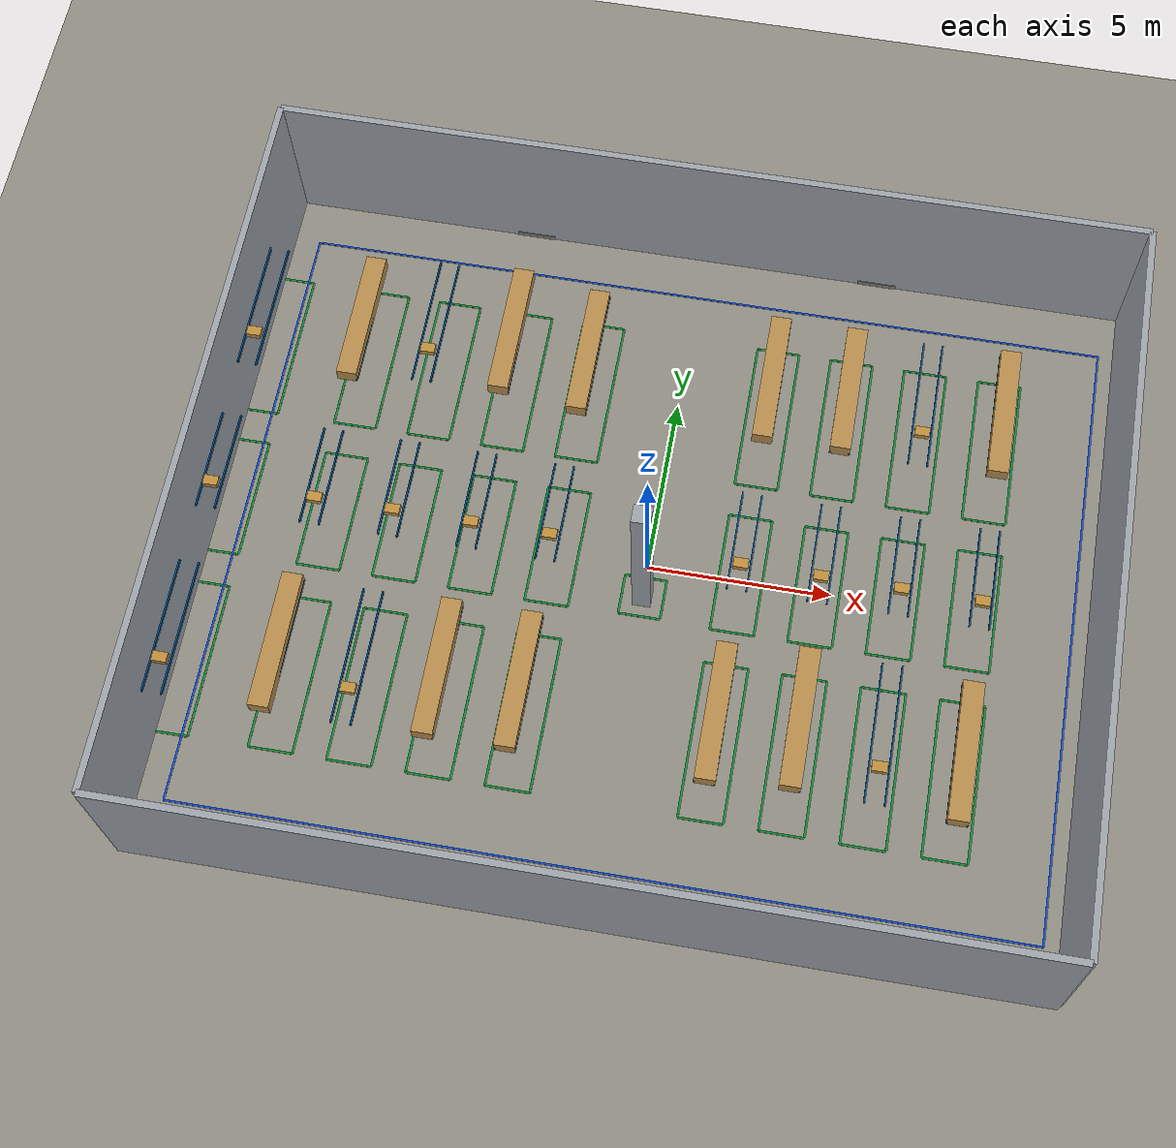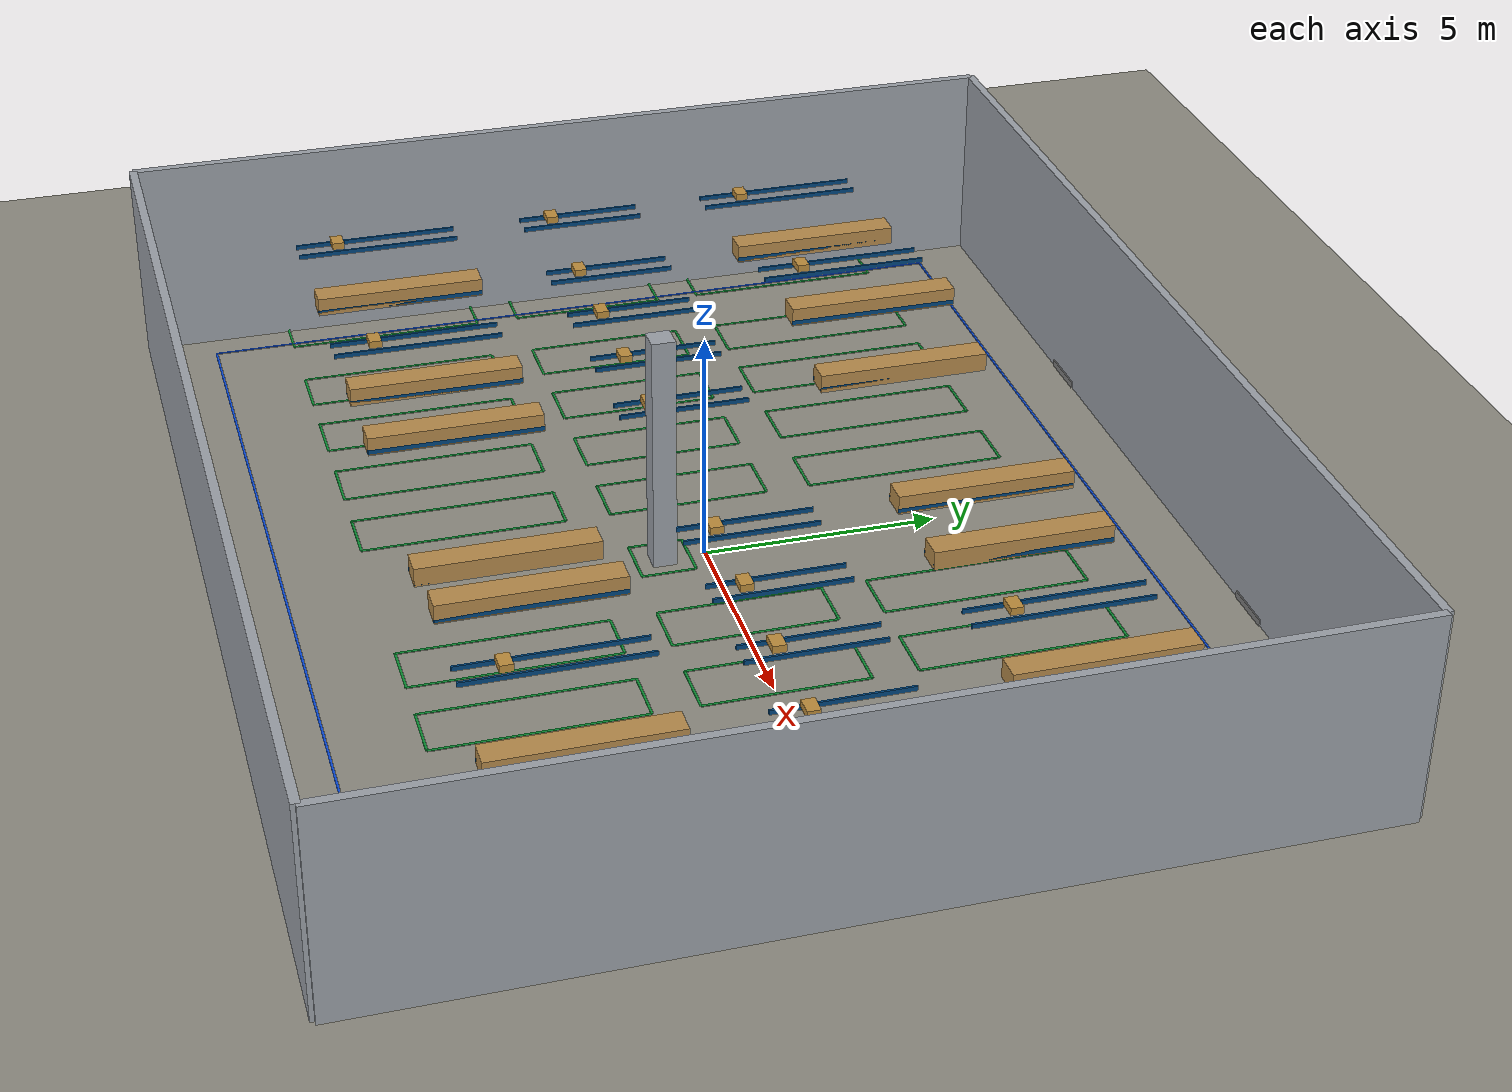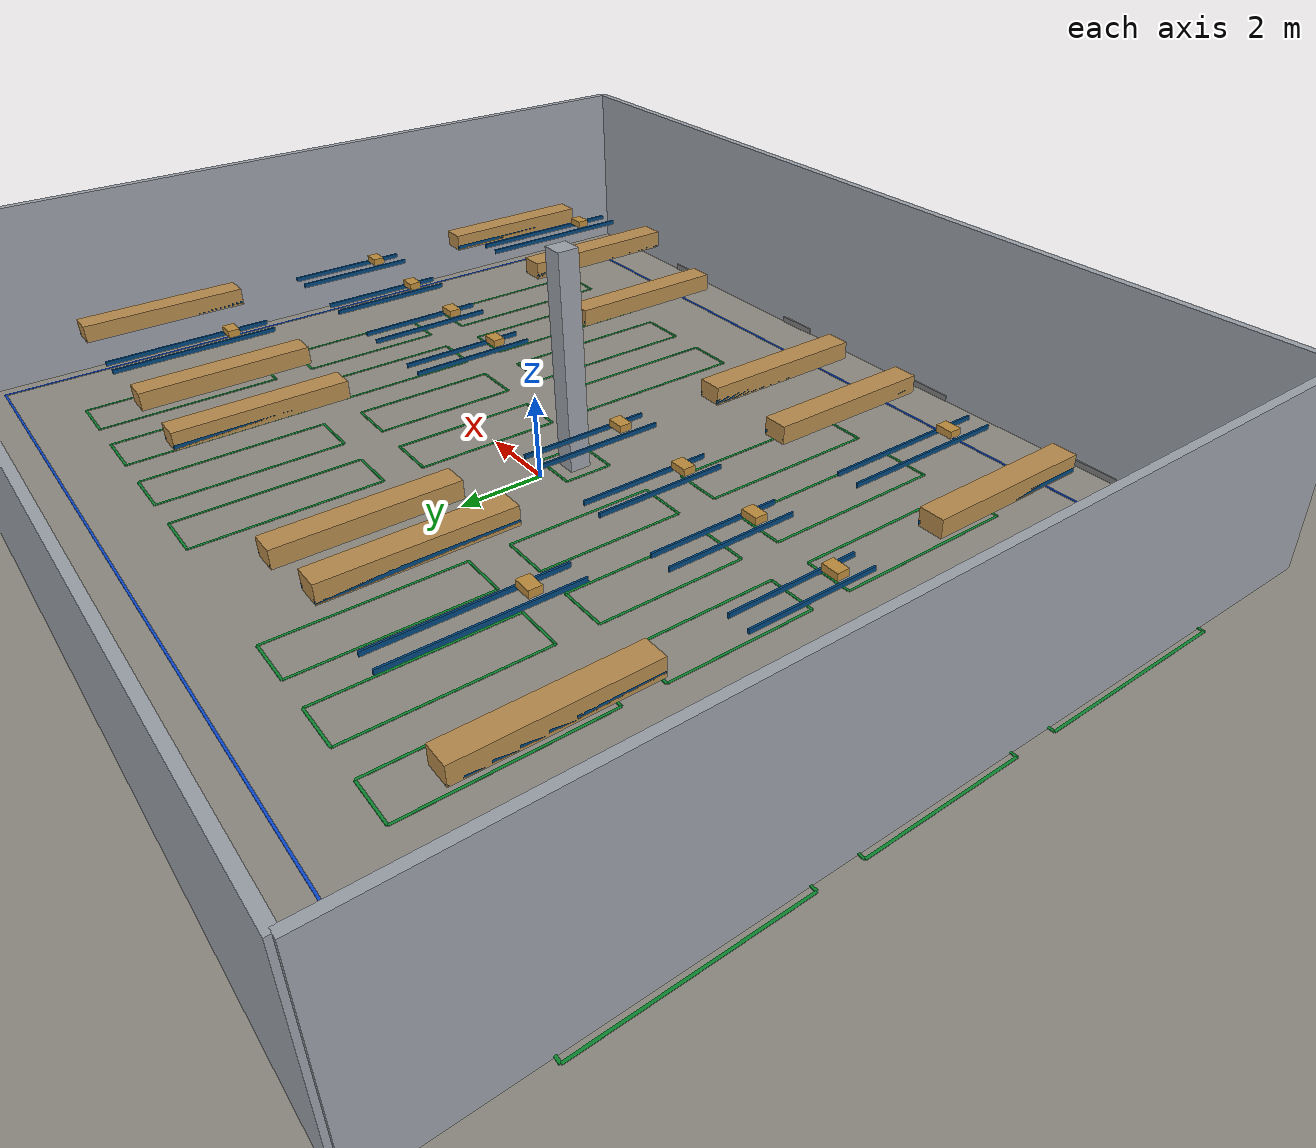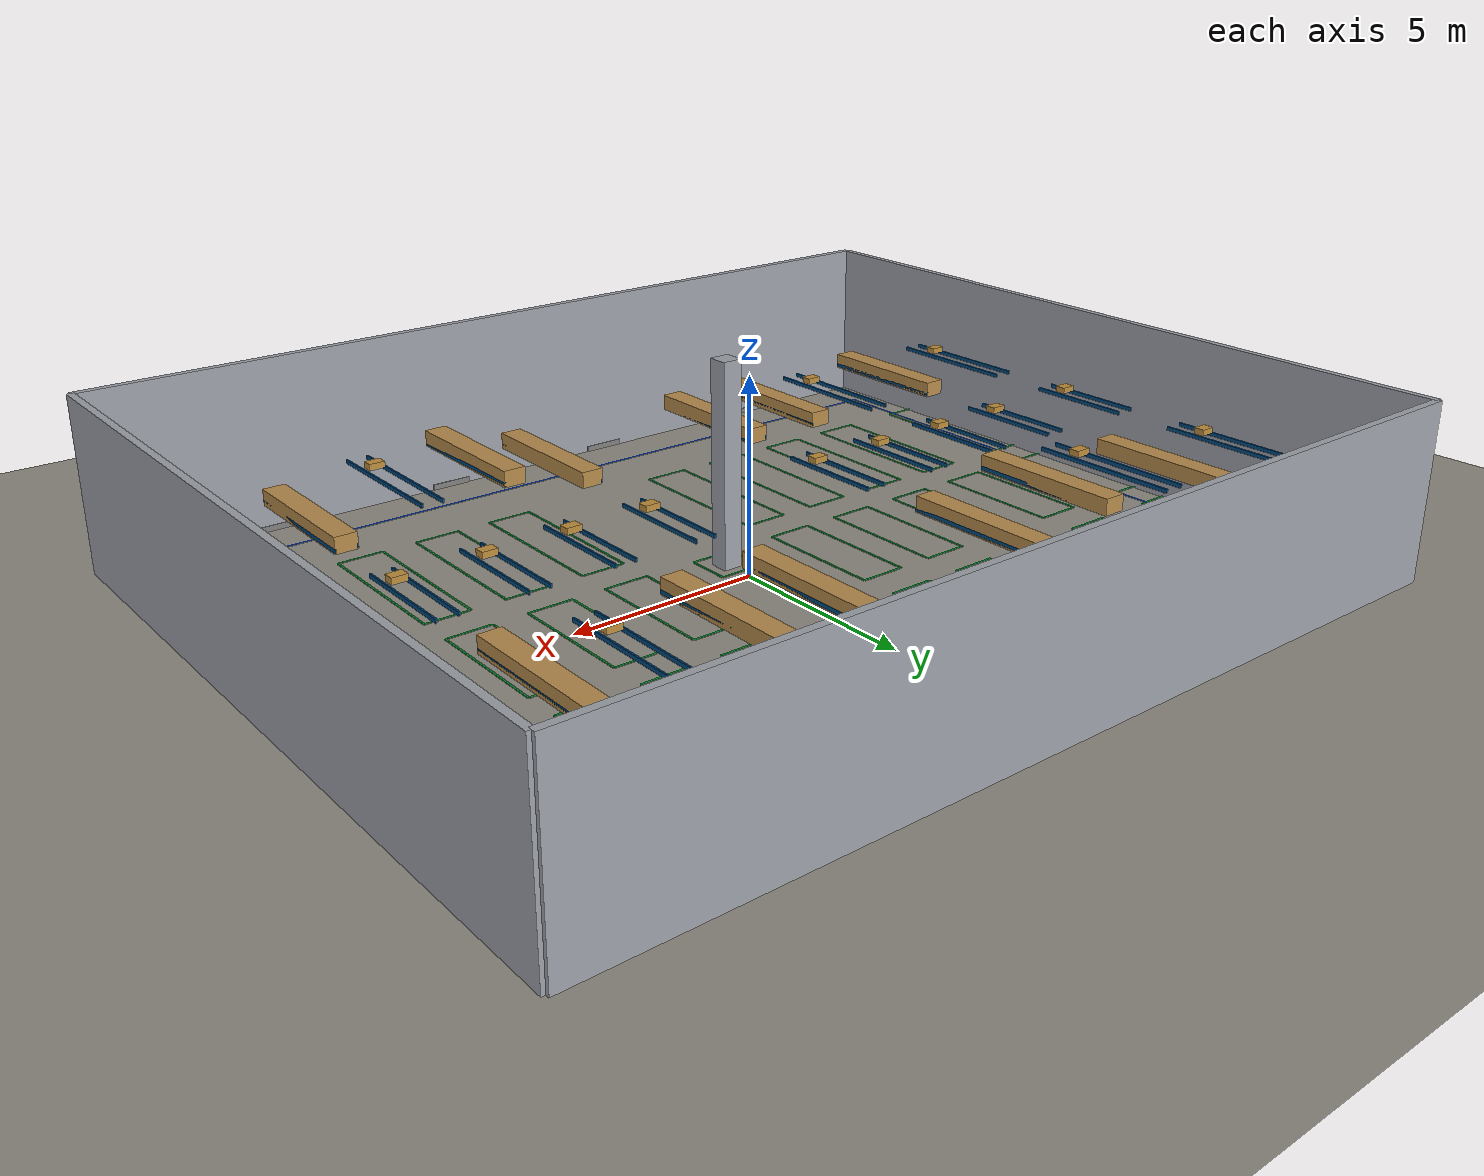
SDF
<sdf version="1.8">
 <world name="warehouse_full_4cam_recfg">
  <physics name="default_physics" type="ode">
   <max_step_size>0.001</max_step_size>
   <real_time_factor>1.0</real_time_factor>
   <real_time_update_rate>1000</real_time_update_rate>
  </physics>
  <plugin name="gz::sim::systems::Physics" filename="gz-sim-physics-system"/>
  <plugin name="gz::sim::systems::UserCommands" filename="gz-sim-user-commands-system"/>
  <plugin name="gz::sim::systems::SceneBroadcaster" filename="gz-sim-scene-broadcaster-system"/>
  <plugin name="gz::sim::systems::Contact" filename="gz-sim-contact-system"/>
  <plugin name="gz::sim::systems::Sensors" filename="gz-sim-sensors-system">
   <render_engine>ogre2</render_engine>
  </plugin>
  <gravity>0 0 -9.81</gravity>
  <magnetic_field>6e-06 2.3e-05 -4.2e-05</magnetic_field>
  <atmosphere type="adiabatic"/>
  <scene>
   <ambient>0.58 0.58 0.58 1</ambient>
   <background>0.70 0.72 0.74 1</background>
   <shadows>true</shadows>
  </scene>
  <model name="ground_plane">
   <static>true</static>
   <link name="link">
    <collision name="collision">
     <geometry><plane><normal>0 0 1</normal><size>24.5 20.5</size></plane></geometry>
    </collision>
    <visual name="visual">
     <geometry><plane><normal>0 0 1</normal><size>24.5 20.5</size></plane></geometry>
     <material>
      <ambient>0.56 0.55 0.51 1</ambient>
      <diffuse>0.56 0.55 0.51 1</diffuse>
      <specular>0.05 0.05 0.05 1</specular>
     </material>
    </visual>
   </link>
  </model>
  <model name="warehouse_walls">
   <static>true</static>
   <link name="wall_east">
    <pose>12.000 0.000 2.250 0 0 0</pose>
    <collision name="collision"><geometry><box><size>0.180 20.000 4.500</size></box></geometry></collision>
    <sensor name="contact" type="contact">
     <contact><collision>collision</collision></contact>
     <update_rate>60</update_rate>
    </sensor>
    <visual name="visual">
     <geometry><box><size>0.180 20.000 4.500</size></box></geometry>
     <material><ambient>0.62 0.64 0.67 1</ambient><diffuse>0.62 0.64 0.67 1</diffuse></material>
    </visual>
   </link>
   <link name="wall_west">
    <pose>-12.000 0.000 2.250 0 0 0</pose>
    <collision name="collision"><geometry><box><size>0.180 20.000 4.500</size></box></geometry></collision>
    <sensor name="contact" type="contact">
     <contact><collision>collision</collision></contact>
     <update_rate>60</update_rate>
    </sensor>
    <visual name="visual">
     <geometry><box><size>0.180 20.000 4.500</size></box></geometry>
     <material><ambient>0.62 0.64 0.67 1</ambient><diffuse>0.62 0.64 0.67 1</diffuse></material>
    </visual>
   </link>
   <link name="wall_north">
    <pose>0.000 10.000 2.250 0 0 0</pose>
    <collision name="collision"><geometry><box><size>24.000 0.180 4.500</size></box></geometry></collision>
    <sensor name="contact" type="contact">
     <contact><collision>collision</collision></contact>
     <update_rate>60</update_rate>
    </sensor>
    <visual name="visual">
     <geometry><box><size>24.000 0.180 4.500</size></box></geometry>
     <material><ambient>0.62 0.64 0.67 1</ambient><diffuse>0.62 0.64 0.67 1</diffuse></material>
    </visual>
   </link>
   <link name="wall_south">
    <pose>0.000 -10.000 2.250 0 0 0</pose>
    <collision name="collision"><geometry><box><size>24.000 0.180 4.500</size></box></geometry></collision>
    <sensor name="contact" type="contact">
     <contact><collision>collision</collision></contact>
     <update_rate>60</update_rate>
    </sensor>
    <visual name="visual">
     <geometry><box><size>24.000 0.180 4.500</size></box></geometry>
     <material><ambient>0.62 0.64 0.67 1</ambient><diffuse>0.62 0.64 0.67 1</diffuse></material>
    </visual>
   </link>
   <link name="south_dock_a">
    <pose>-7.500 -9.920 0.075 0 0 0</pose>
    <visual name="visual">
     <geometry><box><size>1.100 0.070 0.150</size></box></geometry>
     <material><ambient>0.50 0.50 0.50 1</ambient><diffuse>0.50 0.50 0.50 1</diffuse></material>
    </visual>
   </link>
   <link name="south_dock_b">
    <pose>-2.500 -9.920 0.075 0 0 0</pose>
    <visual name="visual">
     <geometry><box><size>1.100 0.070 0.150</size></box></geometry>
     <material><ambient>0.50 0.50 0.50 1</ambient><diffuse>0.50 0.50 0.50 1</diffuse></material>
    </visual>
   </link>
   <link name="south_dock_c">
    <pose>2.500 -9.920 0.075 0 0 0</pose>
    <visual name="visual">
     <geometry><box><size>1.100 0.070 0.150</size></box></geometry>
     <material><ambient>0.50 0.50 0.50 1</ambient><diffuse>0.50 0.50 0.50 1</diffuse></material>
    </visual>
   </link>
   <link name="south_dock_d">
    <pose>7.500 -9.920 0.075 0 0 0</pose>
    <visual name="visual">
     <geometry><box><size>1.100 0.070 0.150</size></box></geometry>
     <material><ambient>0.50 0.50 0.50 1</ambient><diffuse>0.50 0.50 0.50 1</diffuse></material>
    </visual>
   </link>
   <link name="north_dock_a">
    <pose>-5.000 9.920 0.075 0 0 0</pose>
    <visual name="visual">
     <geometry><box><size>1.100 0.070 0.150</size></box></geometry>
     <material><ambient>0.50 0.50 0.50 1</ambient><diffuse>0.50 0.50 0.50 1</diffuse></material>
    </visual>
   </link>
   <link name="north_dock_b">
    <pose>5.000 9.920 0.075 0 0 0</pose>
    <visual name="visual">
     <geometry><box><size>1.100 0.070 0.150</size></box></geometry>
     <material><ambient>0.50 0.50 0.50 1</ambient><diffuse>0.50 0.50 0.50 1</diffuse></material>
    </visual>
   </link>
  </model>
  <model name="warehouse_rack_occluders">
   <static>true</static>
   <link name="stock_rack_W1_south">
    <pose>-8.825 -4.650 2.290 0 0 0</pose>
    <collision name="collision"><geometry><box><size>0.550 3.700 0.400</size></box></geometry></collision>
    <visual name="visual">
     <geometry><box><size>0.550 3.700 0.400</size></box></geometry>
     <material><ambient>0.72 0.55 0.30 1</ambient><diffuse>0.72 0.55 0.30 1</diffuse></material>
    </visual>
   </link>
   <link name="stock_rack_E4_south">
    <pose>8.825 -4.650 2.290 0 0 0</pose>
    <collision name="collision"><geometry><box><size>0.550 3.700 0.400</size></box></geometry></collision>
    <visual name="visual">
     <geometry><box><size>0.550 3.700 0.400</size></box></geometry>
     <material><ambient>0.72 0.55 0.30 1</ambient><diffuse>0.72 0.55 0.30 1</diffuse></material>
    </visual>
   </link>
   <link name="stock_rack_W1_north">
    <pose>-8.825 5.050 2.290 0 0 0</pose>
    <collision name="collision"><geometry><box><size>0.550 3.700 0.400</size></box></geometry></collision>
    <visual name="visual">
     <geometry><box><size>0.550 3.700 0.400</size></box></geometry>
     <material><ambient>0.72 0.55 0.30 1</ambient><diffuse>0.72 0.55 0.30 1</diffuse></material>
    </visual>
   </link>
   <link name="stock_rack_E4_north">
    <pose>8.825 5.050 2.290 0 0 0</pose>
    <collision name="collision"><geometry><box><size>0.550 3.700 0.400</size></box></geometry></collision>
    <visual name="visual">
     <geometry><box><size>0.550 3.700 0.400</size></box></geometry>
     <material><ambient>0.72 0.55 0.30 1</ambient><diffuse>0.72 0.55 0.30 1</diffuse></material>
    </visual>
   </link>
   <link name="stock_rack_W4_north">
    <pose>-2.525 5.050 2.290 0 0 0</pose>
    <collision name="collision"><geometry><box><size>0.550 3.700 0.400</size></box></geometry></collision>
    <visual name="visual">
     <geometry><box><size>0.550 3.700 0.400</size></box></geometry>
     <material><ambient>0.72 0.55 0.30 1</ambient><diffuse>0.72 0.55 0.30 1</diffuse></material>
    </visual>
   </link>
   <link name="stock_rack_E1_north">
    <pose>2.525 5.050 2.290 0 0 0</pose>
    <collision name="collision"><geometry><box><size>0.550 3.700 0.400</size></box></geometry></collision>
    <visual name="visual">
     <geometry><box><size>0.550 3.700 0.400</size></box></geometry>
     <material><ambient>0.72 0.55 0.30 1</ambient><diffuse>0.72 0.55 0.30 1</diffuse></material>
    </visual>
   </link>
   <link name="stock_rack_W4_south">
    <pose>-2.525 -4.650 2.290 0 0 0</pose>
    <collision name="collision"><geometry><box><size>0.550 3.700 0.400</size></box></geometry></collision>
    <visual name="visual">
     <geometry><box><size>0.550 3.700 0.400</size></box></geometry>
     <material><ambient>0.72 0.55 0.30 1</ambient><diffuse>0.72 0.55 0.30 1</diffuse></material>
    </visual>
   </link>
   <link name="stock_rack_E1_south">
    <pose>2.525 -4.650 2.290 0 0 0</pose>
    <collision name="collision"><geometry><box><size>0.550 3.700 0.400</size></box></geometry></collision>
    <visual name="visual">
     <geometry><box><size>0.550 3.700 0.400</size></box></geometry>
     <material><ambient>0.72 0.55 0.30 1</ambient><diffuse>0.72 0.55 0.30 1</diffuse></material>
    </visual>
   </link>
   <link name="stock_rack_E2_south">
    <pose>4.625 -4.650 2.810 0 0 0</pose>
    <collision name="collision"><geometry><box><size>0.550 3.700 0.400</size></box></geometry></collision>
    <visual name="visual">
     <geometry><box><size>0.550 3.700 0.400</size></box></geometry>
     <material><ambient>0.72 0.55 0.30 1</ambient><diffuse>0.72 0.55 0.30 1</diffuse></material>
    </visual>
   </link>
   <link name="stock_rack_W3_north">
    <pose>-4.625 5.050 2.810 0 0 0</pose>
    <collision name="collision"><geometry><box><size>0.550 3.700 0.400</size></box></geometry></collision>
    <visual name="visual">
     <geometry><box><size>0.550 3.700 0.400</size></box></geometry>
     <material><ambient>0.72 0.55 0.30 1</ambient><diffuse>0.72 0.55 0.30 1</diffuse></material>
    </visual>
   </link>
   <link name="stock_rack_W3_south">
    <pose>-4.625 -4.650 2.290 0 0 0</pose>
    <collision name="collision"><geometry><box><size>0.550 3.700 0.400</size></box></geometry></collision>
    <visual name="visual">
     <geometry><box><size>0.550 3.700 0.400</size></box></geometry>
     <material><ambient>0.72 0.55 0.30 1</ambient><diffuse>0.72 0.55 0.30 1</diffuse></material>
    </visual>
   </link>
   <link name="stock_rack_E2_north">
    <pose>4.625 5.050 2.290 0 0 0</pose>
    <collision name="collision"><geometry><box><size>0.550 3.700 0.400</size></box></geometry></collision>
    <visual name="visual">
     <geometry><box><size>0.550 3.700 0.400</size></box></geometry>
     <material><ambient>0.72 0.55 0.30 1</ambient><diffuse>0.72 0.55 0.30 1</diffuse></material>
    </visual>
   </link>
   <link name="rack_W1_south">
    <pose>-8.825 -4.650 1.045 0 0 0</pose>
    <collision name="collision"><geometry><box><size>0.550 3.700 2.090</size></box></geometry></collision>
    <sensor name="contact" type="contact">
     <contact><collision>collision</collision></contact>
     <update_rate>60</update_rate>
    </sensor>
   </link>
   <link name="rail_W1_south_west">
    <pose>-9.080 -4.650 2.160 0 0 0</pose>
    <visual name="visual">
     <geometry><box><size>0.040 3.700 0.100</size></box></geometry>
     <material><ambient>0.00 0.28 0.50 1</ambient><diffuse>0.00 0.28 0.50 1</diffuse></material>
    </visual>
   </link>
   <link name="rail_W1_south_east">
    <pose>-8.570 -4.650 2.160 0 0 0</pose>
    <visual name="visual">
     <geometry><box><size>0.040 3.700 0.100</size></box></geometry>
     <material><ambient>0.00 0.28 0.50 1</ambient><diffuse>0.00 0.28 0.50 1</diffuse></material>
    </visual>
   </link>
   <link name="shelfbox_W1_south">
    <pose>-8.825 -5.575 2.290 0 0 0</pose>
    <visual name="visual">
     <geometry><box><size>0.390 0.270 0.160</size></box></geometry>
     <material><ambient>0.75 0.56 0.24 1</ambient><diffuse>0.75 0.56 0.24 1</diffuse></material>
    </visual>
   </link>
   <link name="rack_W1_mid">
    <pose>-8.825 0.200 1.045 0 0 0</pose>
    <collision name="collision"><geometry><box><size>0.550 2.800 2.090</size></box></geometry></collision>
    <sensor name="contact" type="contact">
     <contact><collision>collision</collision></contact>
     <update_rate>60</update_rate>
    </sensor>
   </link>
   <link name="rail_W1_mid_west">
    <pose>-9.080 0.200 2.160 0 0 0</pose>
    <visual name="visual">
     <geometry><box><size>0.040 2.800 0.100</size></box></geometry>
     <material><ambient>0.00 0.28 0.50 1</ambient><diffuse>0.00 0.28 0.50 1</diffuse></material>
    </visual>
   </link>
   <link name="rail_W1_mid_east">
    <pose>-8.570 0.200 2.160 0 0 0</pose>
    <visual name="visual">
     <geometry><box><size>0.040 2.800 0.100</size></box></geometry>
     <material><ambient>0.00 0.28 0.50 1</ambient><diffuse>0.00 0.28 0.50 1</diffuse></material>
    </visual>
   </link>
   <link name="shelfbox_W1_mid">
    <pose>-8.825 -0.500 2.290 0 0 0</pose>
    <visual name="visual">
     <geometry><box><size>0.390 0.270 0.160</size></box></geometry>
     <material><ambient>0.75 0.56 0.24 1</ambient><diffuse>0.75 0.56 0.24 1</diffuse></material>
    </visual>
   </link>
   <link name="rack_W1_north">
    <pose>-8.825 5.050 1.045 0 0 0</pose>
    <collision name="collision"><geometry><box><size>0.550 3.700 2.090</size></box></geometry></collision>
    <sensor name="contact" type="contact">
     <contact><collision>collision</collision></contact>
     <update_rate>60</update_rate>
    </sensor>
   </link>
   <link name="rail_W1_north_west">
    <pose>-9.080 5.050 2.160 0 0 0</pose>
    <visual name="visual">
     <geometry><box><size>0.040 3.700 0.100</size></box></geometry>
     <material><ambient>0.00 0.28 0.50 1</ambient><diffuse>0.00 0.28 0.50 1</diffuse></material>
    </visual>
   </link>
   <link name="rail_W1_north_east">
    <pose>-8.570 5.050 2.160 0 0 0</pose>
    <visual name="visual">
     <geometry><box><size>0.040 3.700 0.100</size></box></geometry>
     <material><ambient>0.00 0.28 0.50 1</ambient><diffuse>0.00 0.28 0.50 1</diffuse></material>
    </visual>
   </link>
   <link name="shelfbox_W1_north">
    <pose>-8.825 4.125 2.290 0 0 0</pose>
    <visual name="visual">
     <geometry><box><size>0.390 0.270 0.160</size></box></geometry>
     <material><ambient>0.75 0.56 0.24 1</ambient><diffuse>0.75 0.56 0.24 1</diffuse></material>
    </visual>
   </link>
   <link name="rack_W2_south">
    <pose>-6.725 -4.650 1.045 0 0 0</pose>
    <collision name="collision"><geometry><box><size>0.550 3.700 2.090</size></box></geometry></collision>
    <sensor name="contact" type="contact">
     <contact><collision>collision</collision></contact>
     <update_rate>60</update_rate>
    </sensor>
   </link>
   <link name="rail_W2_south_west">
    <pose>-6.980 -4.650 2.160 0 0 0</pose>
    <visual name="visual">
     <geometry><box><size>0.040 3.700 0.100</size></box></geometry>
     <material><ambient>0.00 0.28 0.50 1</ambient><diffuse>0.00 0.28 0.50 1</diffuse></material>
    </visual>
   </link>
   <link name="rail_W2_south_east">
    <pose>-6.470 -4.650 2.160 0 0 0</pose>
    <visual name="visual">
     <geometry><box><size>0.040 3.700 0.100</size></box></geometry>
     <material><ambient>0.00 0.28 0.50 1</ambient><diffuse>0.00 0.28 0.50 1</diffuse></material>
    </visual>
   </link>
   <link name="shelfbox_W2_south">
    <pose>-6.725 -5.575 2.290 0 0 0</pose>
    <visual name="visual">
     <geometry><box><size>0.390 0.270 0.160</size></box></geometry>
     <material><ambient>0.75 0.56 0.24 1</ambient><diffuse>0.75 0.56 0.24 1</diffuse></material>
    </visual>
   </link>
   <link name="rack_W2_mid">
    <pose>-6.725 0.200 1.045 0 0 0</pose>
    <collision name="collision"><geometry><box><size>0.550 2.800 2.090</size></box></geometry></collision>
    <sensor name="contact" type="contact">
     <contact><collision>collision</collision></contact>
     <update_rate>60</update_rate>
    </sensor>
   </link>
   <link name="rail_W2_mid_west">
    <pose>-6.980 0.200 2.160 0 0 0</pose>
    <visual name="visual">
     <geometry><box><size>0.040 2.800 0.100</size></box></geometry>
     <material><ambient>0.00 0.28 0.50 1</ambient><diffuse>0.00 0.28 0.50 1</diffuse></material>
    </visual>
   </link>
   <link name="rail_W2_mid_east">
    <pose>-6.470 0.200 2.160 0 0 0</pose>
    <visual name="visual">
     <geometry><box><size>0.040 2.800 0.100</size></box></geometry>
     <material><ambient>0.00 0.28 0.50 1</ambient><diffuse>0.00 0.28 0.50 1</diffuse></material>
    </visual>
   </link>
   <link name="shelfbox_W2_mid">
    <pose>-6.725 -0.500 2.290 0 0 0</pose>
    <visual name="visual">
     <geometry><box><size>0.390 0.270 0.160</size></box></geometry>
     <material><ambient>0.75 0.56 0.24 1</ambient><diffuse>0.75 0.56 0.24 1</diffuse></material>
    </visual>
   </link>
   <link name="rack_W2_north">
    <pose>-6.725 5.050 1.305 0 0 0</pose>
    <collision name="collision"><geometry><box><size>0.550 3.700 2.610</size></box></geometry></collision>
    <sensor name="contact" type="contact">
     <contact><collision>collision</collision></contact>
     <update_rate>60</update_rate>
    </sensor>
   </link>
   <link name="rail_W2_north_west">
    <pose>-6.980 5.050 2.680 0 0 0</pose>
    <visual name="visual">
     <geometry><box><size>0.040 3.700 0.100</size></box></geometry>
     <material><ambient>0.00 0.28 0.50 1</ambient><diffuse>0.00 0.28 0.50 1</diffuse></material>
    </visual>
   </link>
   <link name="rail_W2_north_east">
    <pose>-6.470 5.050 2.680 0 0 0</pose>
    <visual name="visual">
     <geometry><box><size>0.040 3.700 0.100</size></box></geometry>
     <material><ambient>0.00 0.28 0.50 1</ambient><diffuse>0.00 0.28 0.50 1</diffuse></material>
    </visual>
   </link>
   <link name="shelfbox_W2_north">
    <pose>-6.725 4.125 2.810 0 0 0</pose>
    <visual name="visual">
     <geometry><box><size>0.390 0.270 0.160</size></box></geometry>
     <material><ambient>0.75 0.56 0.24 1</ambient><diffuse>0.75 0.56 0.24 1</diffuse></material>
    </visual>
   </link>
   <link name="rack_W3_south">
    <pose>-4.625 -4.650 1.045 0 0 0</pose>
    <collision name="collision"><geometry><box><size>0.550 3.700 2.090</size></box></geometry></collision>
    <sensor name="contact" type="contact">
     <contact><collision>collision</collision></contact>
     <update_rate>60</update_rate>
    </sensor>
   </link>
   <link name="rail_W3_south_west">
    <pose>-4.880 -4.650 2.160 0 0 0</pose>
    <visual name="visual">
     <geometry><box><size>0.040 3.700 0.100</size></box></geometry>
     <material><ambient>0.00 0.28 0.50 1</ambient><diffuse>0.00 0.28 0.50 1</diffuse></material>
    </visual>
   </link>
   <link name="rail_W3_south_east">
    <pose>-4.370 -4.650 2.160 0 0 0</pose>
    <visual name="visual">
     <geometry><box><size>0.040 3.700 0.100</size></box></geometry>
     <material><ambient>0.00 0.28 0.50 1</ambient><diffuse>0.00 0.28 0.50 1</diffuse></material>
    </visual>
   </link>
   <link name="shelfbox_W3_south">
    <pose>-4.625 -5.575 2.290 0 0 0</pose>
    <visual name="visual">
     <geometry><box><size>0.390 0.270 0.160</size></box></geometry>
     <material><ambient>0.75 0.56 0.24 1</ambient><diffuse>0.75 0.56 0.24 1</diffuse></material>
    </visual>
   </link>
   <link name="rack_W3_mid">
    <pose>-4.625 0.200 1.045 0 0 0</pose>
    <collision name="collision"><geometry><box><size>0.550 2.800 2.090</size></box></geometry></collision>
    <sensor name="contact" type="contact">
     <contact><collision>collision</collision></contact>
     <update_rate>60</update_rate>
    </sensor>
   </link>
   <link name="rail_W3_mid_west">
    <pose>-4.880 0.200 2.160 0 0 0</pose>
    <visual name="visual">
     <geometry><box><size>0.040 2.800 0.100</size></box></geometry>
     <material><ambient>0.00 0.28 0.50 1</ambient><diffuse>0.00 0.28 0.50 1</diffuse></material>
    </visual>
   </link>
   <link name="rail_W3_mid_east">
    <pose>-4.370 0.200 2.160 0 0 0</pose>
    <visual name="visual">
     <geometry><box><size>0.040 2.800 0.100</size></box></geometry>
     <material><ambient>0.00 0.28 0.50 1</ambient><diffuse>0.00 0.28 0.50 1</diffuse></material>
    </visual>
   </link>
   <link name="shelfbox_W3_mid">
    <pose>-4.625 -0.500 2.290 0 0 0</pose>
    <visual name="visual">
     <geometry><box><size>0.390 0.270 0.160</size></box></geometry>
     <material><ambient>0.75 0.56 0.24 1</ambient><diffuse>0.75 0.56 0.24 1</diffuse></material>
    </visual>
   </link>
   <link name="rack_W3_north">
    <pose>-4.625 5.050 1.305 0 0 0</pose>
    <collision name="collision"><geometry><box><size>0.550 3.700 2.610</size></box></geometry></collision>
    <sensor name="contact" type="contact">
     <contact><collision>collision</collision></contact>
     <update_rate>60</update_rate>
    </sensor>
   </link>
   <link name="rail_W3_north_west">
    <pose>-4.880 5.050 2.680 0 0 0</pose>
    <visual name="visual">
     <geometry><box><size>0.040 3.700 0.100</size></box></geometry>
     <material><ambient>0.00 0.28 0.50 1</ambient><diffuse>0.00 0.28 0.50 1</diffuse></material>
    </visual>
   </link>
   <link name="rail_W3_north_east">
    <pose>-4.370 5.050 2.680 0 0 0</pose>
    <visual name="visual">
     <geometry><box><size>0.040 3.700 0.100</size></box></geometry>
     <material><ambient>0.00 0.28 0.50 1</ambient><diffuse>0.00 0.28 0.50 1</diffuse></material>
    </visual>
   </link>
   <link name="shelfbox_W3_north">
    <pose>-4.625 4.125 2.810 0 0 0</pose>
    <visual name="visual">
     <geometry><box><size>0.390 0.270 0.160</size></box></geometry>
     <material><ambient>0.75 0.56 0.24 1</ambient><diffuse>0.75 0.56 0.24 1</diffuse></material>
    </visual>
   </link>
   <link name="rack_W4_south">
    <pose>-2.525 -4.650 1.045 0 0 0</pose>
    <collision name="collision"><geometry><box><size>0.550 3.700 2.090</size></box></geometry></collision>
    <sensor name="contact" type="contact">
     <contact><collision>collision</collision></contact>
     <update_rate>60</update_rate>
    </sensor>
   </link>
   <link name="rail_W4_south_west">
    <pose>-2.780 -4.650 2.160 0 0 0</pose>
    <visual name="visual">
     <geometry><box><size>0.040 3.700 0.100</size></box></geometry>
     <material><ambient>0.00 0.28 0.50 1</ambient><diffuse>0.00 0.28 0.50 1</diffuse></material>
    </visual>
   </link>
   <link name="rail_W4_south_east">
    <pose>-2.270 -4.650 2.160 0 0 0</pose>
    <visual name="visual">
     <geometry><box><size>0.040 3.700 0.100</size></box></geometry>
     <material><ambient>0.00 0.28 0.50 1</ambient><diffuse>0.00 0.28 0.50 1</diffuse></material>
    </visual>
   </link>
   <link name="shelfbox_W4_south">
    <pose>-2.525 -5.575 2.290 0 0 0</pose>
    <visual name="visual">
     <geometry><box><size>0.390 0.270 0.160</size></box></geometry>
     <material><ambient>0.75 0.56 0.24 1</ambient><diffuse>0.75 0.56 0.24 1</diffuse></material>
    </visual>
   </link>
   <link name="rack_W4_mid">
    <pose>-2.525 0.200 1.045 0 0 0</pose>
    <collision name="collision"><geometry><box><size>0.550 2.800 2.090</size></box></geometry></collision>
    <sensor name="contact" type="contact">
     <contact><collision>collision</collision></contact>
     <update_rate>60</update_rate>
    </sensor>
   </link>
   <link name="rail_W4_mid_west">
    <pose>-2.780 0.200 2.160 0 0 0</pose>
    <visual name="visual">
     <geometry><box><size>0.040 2.800 0.100</size></box></geometry>
     <material><ambient>0.00 0.28 0.50 1</ambient><diffuse>0.00 0.28 0.50 1</diffuse></material>
    </visual>
   </link>
   <link name="rail_W4_mid_east">
    <pose>-2.270 0.200 2.160 0 0 0</pose>
    <visual name="visual">
     <geometry><box><size>0.040 2.800 0.100</size></box></geometry>
     <material><ambient>0.00 0.28 0.50 1</ambient><diffuse>0.00 0.28 0.50 1</diffuse></material>
    </visual>
   </link>
   <link name="shelfbox_W4_mid">
    <pose>-2.525 -0.500 2.290 0 0 0</pose>
    <visual name="visual">
     <geometry><box><size>0.390 0.270 0.160</size></box></geometry>
     <material><ambient>0.75 0.56 0.24 1</ambient><diffuse>0.75 0.56 0.24 1</diffuse></material>
    </visual>
   </link>
   <link name="rack_W4_north">
    <pose>-2.525 5.050 1.045 0 0 0</pose>
    <collision name="collision"><geometry><box><size>0.550 3.700 2.090</size></box></geometry></collision>
    <sensor name="contact" type="contact">
     <contact><collision>collision</collision></contact>
     <update_rate>60</update_rate>
    </sensor>
   </link>
   <link name="rail_W4_north_west">
    <pose>-2.780 5.050 2.160 0 0 0</pose>
    <visual name="visual">
     <geometry><box><size>0.040 3.700 0.100</size></box></geometry>
     <material><ambient>0.00 0.28 0.50 1</ambient><diffuse>0.00 0.28 0.50 1</diffuse></material>
    </visual>
   </link>
   <link name="rail_W4_north_east">
    <pose>-2.270 5.050 2.160 0 0 0</pose>
    <visual name="visual">
     <geometry><box><size>0.040 3.700 0.100</size></box></geometry>
     <material><ambient>0.00 0.28 0.50 1</ambient><diffuse>0.00 0.28 0.50 1</diffuse></material>
    </visual>
   </link>
   <link name="shelfbox_W4_north">
    <pose>-2.525 4.125 2.290 0 0 0</pose>
    <visual name="visual">
     <geometry><box><size>0.390 0.270 0.160</size></box></geometry>
     <material><ambient>0.75 0.56 0.24 1</ambient><diffuse>0.75 0.56 0.24 1</diffuse></material>
    </visual>
   </link>
   <link name="rack_E1_south">
    <pose>2.525 -4.650 1.045 0 0 0</pose>
    <collision name="collision"><geometry><box><size>0.550 3.700 2.090</size></box></geometry></collision>
    <sensor name="contact" type="contact">
     <contact><collision>collision</collision></contact>
     <update_rate>60</update_rate>
    </sensor>
   </link>
   <link name="rail_E1_south_west">
    <pose>2.270 -4.650 2.160 0 0 0</pose>
    <visual name="visual">
     <geometry><box><size>0.040 3.700 0.100</size></box></geometry>
     <material><ambient>0.00 0.28 0.50 1</ambient><diffuse>0.00 0.28 0.50 1</diffuse></material>
    </visual>
   </link>
   <link name="rail_E1_south_east">
    <pose>2.780 -4.650 2.160 0 0 0</pose>
    <visual name="visual">
     <geometry><box><size>0.040 3.700 0.100</size></box></geometry>
     <material><ambient>0.00 0.28 0.50 1</ambient><diffuse>0.00 0.28 0.50 1</diffuse></material>
    </visual>
   </link>
   <link name="shelfbox_E1_south">
    <pose>2.525 -5.575 2.290 0 0 0</pose>
    <visual name="visual">
     <geometry><box><size>0.390 0.270 0.160</size></box></geometry>
     <material><ambient>0.75 0.56 0.24 1</ambient><diffuse>0.75 0.56 0.24 1</diffuse></material>
    </visual>
   </link>
   <link name="rack_E1_mid">
    <pose>2.525 0.200 1.045 0 0 0</pose>
    <collision name="collision"><geometry><box><size>0.550 2.800 2.090</size></box></geometry></collision>
    <sensor name="contact" type="contact">
     <contact><collision>collision</collision></contact>
     <update_rate>60</update_rate>
    </sensor>
   </link>
   <link name="rail_E1_mid_west">
    <pose>2.270 0.200 2.160 0 0 0</pose>
    <visual name="visual">
     <geometry><box><size>0.040 2.800 0.100</size></box></geometry>
     <material><ambient>0.00 0.28 0.50 1</ambient><diffuse>0.00 0.28 0.50 1</diffuse></material>
    </visual>
   </link>
   <link name="rail_E1_mid_east">
    <pose>2.780 0.200 2.160 0 0 0</pose>
    <visual name="visual">
     <geometry><box><size>0.040 2.800 0.100</size></box></geometry>
     <material><ambient>0.00 0.28 0.50 1</ambient><diffuse>0.00 0.28 0.50 1</diffuse></material>
    </visual>
   </link>
   <link name="shelfbox_E1_mid">
    <pose>2.525 -0.500 2.290 0 0 0</pose>
    <visual name="visual">
     <geometry><box><size>0.390 0.270 0.160</size></box></geometry>
     <material><ambient>0.75 0.56 0.24 1</ambient><diffuse>0.75 0.56 0.24 1</diffuse></material>
    </visual>
   </link>
   <link name="rack_E1_north">
    <pose>2.525 5.050 1.045 0 0 0</pose>
    <collision name="collision"><geometry><box><size>0.550 3.700 2.090</size></box></geometry></collision>
    <sensor name="contact" type="contact">
     <contact><collision>collision</collision></contact>
     <update_rate>60</update_rate>
    </sensor>
   </link>
   <link name="rail_E1_north_west">
    <pose>2.270 5.050 2.160 0 0 0</pose>
    <visual name="visual">
     <geometry><box><size>0.040 3.700 0.100</size></box></geometry>
     <material><ambient>0.00 0.28 0.50 1</ambient><diffuse>0.00 0.28 0.50 1</diffuse></material>
    </visual>
   </link>
   <link name="rail_E1_north_east">
    <pose>2.780 5.050 2.160 0 0 0</pose>
    <visual name="visual">
     <geometry><box><size>0.040 3.700 0.100</size></box></geometry>
     <material><ambient>0.00 0.28 0.50 1</ambient><diffuse>0.00 0.28 0.50 1</diffuse></material>
    </visual>
   </link>
   <link name="shelfbox_E1_north">
    <pose>2.525 4.125 2.290 0 0 0</pose>
    <visual name="visual">
     <geometry><box><size>0.390 0.270 0.160</size></box></geometry>
     <material><ambient>0.75 0.56 0.24 1</ambient><diffuse>0.75 0.56 0.24 1</diffuse></material>
    </visual>
   </link>
   <link name="rack_E2_south">
    <pose>4.625 -4.650 1.305 0 0 0</pose>
    <collision name="collision"><geometry><box><size>0.550 3.700 2.610</size></box></geometry></collision>
    <sensor name="contact" type="contact">
     <contact><collision>collision</collision></contact>
     <update_rate>60</update_rate>
    </sensor>
   </link>
   <link name="rail_E2_south_west">
    <pose>4.370 -4.650 2.680 0 0 0</pose>
    <visual name="visual">
     <geometry><box><size>0.040 3.700 0.100</size></box></geometry>
     <material><ambient>0.00 0.28 0.50 1</ambient><diffuse>0.00 0.28 0.50 1</diffuse></material>
    </visual>
   </link>
   <link name="rail_E2_south_east">
    <pose>4.880 -4.650 2.680 0 0 0</pose>
    <visual name="visual">
     <geometry><box><size>0.040 3.700 0.100</size></box></geometry>
     <material><ambient>0.00 0.28 0.50 1</ambient><diffuse>0.00 0.28 0.50 1</diffuse></material>
    </visual>
   </link>
   <link name="shelfbox_E2_south">
    <pose>4.625 -5.575 2.810 0 0 0</pose>
    <visual name="visual">
     <geometry><box><size>0.390 0.270 0.160</size></box></geometry>
     <material><ambient>0.75 0.56 0.24 1</ambient><diffuse>0.75 0.56 0.24 1</diffuse></material>
    </visual>
   </link>
   <link name="rack_E2_mid">
    <pose>4.625 0.200 1.045 0 0 0</pose>
    <collision name="collision"><geometry><box><size>0.550 2.800 2.090</size></box></geometry></collision>
    <sensor name="contact" type="contact">
     <contact><collision>collision</collision></contact>
     <update_rate>60</update_rate>
    </sensor>
   </link>
   <link name="rail_E2_mid_west">
    <pose>4.370 0.200 2.160 0 0 0</pose>
    <visual name="visual">
     <geometry><box><size>0.040 2.800 0.100</size></box></geometry>
     <material><ambient>0.00 0.28 0.50 1</ambient><diffuse>0.00 0.28 0.50 1</diffuse></material>
    </visual>
   </link>
   <link name="rail_E2_mid_east">
    <pose>4.880 0.200 2.160 0 0 0</pose>
    <visual name="visual">
     <geometry><box><size>0.040 2.800 0.100</size></box></geometry>
     <material><ambient>0.00 0.28 0.50 1</ambient><diffuse>0.00 0.28 0.50 1</diffuse></material>
    </visual>
   </link>
   <link name="shelfbox_E2_mid">
    <pose>4.625 -0.500 2.290 0 0 0</pose>
    <visual name="visual">
     <geometry><box><size>0.390 0.270 0.160</size></box></geometry>
     <material><ambient>0.75 0.56 0.24 1</ambient><diffuse>0.75 0.56 0.24 1</diffuse></material>
    </visual>
   </link>
   <link name="rack_E2_north">
    <pose>4.625 5.050 1.045 0 0 0</pose>
    <collision name="collision"><geometry><box><size>0.550 3.700 2.090</size></box></geometry></collision>
    <sensor name="contact" type="contact">
     <contact><collision>collision</collision></contact>
     <update_rate>60</update_rate>
    </sensor>
   </link>
   <link name="rail_E2_north_west">
    <pose>4.370 5.050 2.160 0 0 0</pose>
    <visual name="visual">
     <geometry><box><size>0.040 3.700 0.100</size></box></geometry>
     <material><ambient>0.00 0.28 0.50 1</ambient><diffuse>0.00 0.28 0.50 1</diffuse></material>
    </visual>
   </link>
   <link name="rail_E2_north_east">
    <pose>4.880 5.050 2.160 0 0 0</pose>
    <visual name="visual">
     <geometry><box><size>0.040 3.700 0.100</size></box></geometry>
     <material><ambient>0.00 0.28 0.50 1</ambient><diffuse>0.00 0.28 0.50 1</diffuse></material>
    </visual>
   </link>
   <link name="shelfbox_E2_north">
    <pose>4.625 4.125 2.290 0 0 0</pose>
    <visual name="visual">
     <geometry><box><size>0.390 0.270 0.160</size></box></geometry>
     <material><ambient>0.75 0.56 0.24 1</ambient><diffuse>0.75 0.56 0.24 1</diffuse></material>
    </visual>
   </link>
   <link name="rack_E3_south">
    <pose>6.725 -4.650 1.305 0 0 0</pose>
    <collision name="collision"><geometry><box><size>0.550 3.700 2.610</size></box></geometry></collision>
    <sensor name="contact" type="contact">
     <contact><collision>collision</collision></contact>
     <update_rate>60</update_rate>
    </sensor>
   </link>
   <link name="rail_E3_south_west">
    <pose>6.470 -4.650 2.680 0 0 0</pose>
    <visual name="visual">
     <geometry><box><size>0.040 3.700 0.100</size></box></geometry>
     <material><ambient>0.00 0.28 0.50 1</ambient><diffuse>0.00 0.28 0.50 1</diffuse></material>
    </visual>
   </link>
   <link name="rail_E3_south_east">
    <pose>6.980 -4.650 2.680 0 0 0</pose>
    <visual name="visual">
     <geometry><box><size>0.040 3.700 0.100</size></box></geometry>
     <material><ambient>0.00 0.28 0.50 1</ambient><diffuse>0.00 0.28 0.50 1</diffuse></material>
    </visual>
   </link>
   <link name="shelfbox_E3_south">
    <pose>6.725 -5.575 2.810 0 0 0</pose>
    <visual name="visual">
     <geometry><box><size>0.390 0.270 0.160</size></box></geometry>
     <material><ambient>0.75 0.56 0.24 1</ambient><diffuse>0.75 0.56 0.24 1</diffuse></material>
    </visual>
   </link>
   <link name="rack_E3_mid">
    <pose>6.725 0.200 1.045 0 0 0</pose>
    <collision name="collision"><geometry><box><size>0.550 2.800 2.090</size></box></geometry></collision>
    <sensor name="contact" type="contact">
     <contact><collision>collision</collision></contact>
     <update_rate>60</update_rate>
    </sensor>
   </link>
   <link name="rail_E3_mid_west">
    <pose>6.470 0.200 2.160 0 0 0</pose>
    <visual name="visual">
     <geometry><box><size>0.040 2.800 0.100</size></box></geometry>
     <material><ambient>0.00 0.28 0.50 1</ambient><diffuse>0.00 0.28 0.50 1</diffuse></material>
    </visual>
   </link>
   <link name="rail_E3_mid_east">
    <pose>6.980 0.200 2.160 0 0 0</pose>
    <visual name="visual">
     <geometry><box><size>0.040 2.800 0.100</size></box></geometry>
     <material><ambient>0.00 0.28 0.50 1</ambient><diffuse>0.00 0.28 0.50 1</diffuse></material>
    </visual>
   </link>
   <link name="shelfbox_E3_mid">
    <pose>6.725 -0.500 2.290 0 0 0</pose>
    <visual name="visual">
     <geometry><box><size>0.390 0.270 0.160</size></box></geometry>
     <material><ambient>0.75 0.56 0.24 1</ambient><diffuse>0.75 0.56 0.24 1</diffuse></material>
    </visual>
   </link>
   <link name="rack_E3_north">
    <pose>6.725 5.050 1.045 0 0 0</pose>
    <collision name="collision"><geometry><box><size>0.550 3.700 2.090</size></box></geometry></collision>
    <sensor name="contact" type="contact">
     <contact><collision>collision</collision></contact>
     <update_rate>60</update_rate>
    </sensor>
   </link>
   <link name="rail_E3_north_west">
    <pose>6.470 5.050 2.160 0 0 0</pose>
    <visual name="visual">
     <geometry><box><size>0.040 3.700 0.100</size></box></geometry>
     <material><ambient>0.00 0.28 0.50 1</ambient><diffuse>0.00 0.28 0.50 1</diffuse></material>
    </visual>
   </link>
   <link name="rail_E3_north_east">
    <pose>6.980 5.050 2.160 0 0 0</pose>
    <visual name="visual">
     <geometry><box><size>0.040 3.700 0.100</size></box></geometry>
     <material><ambient>0.00 0.28 0.50 1</ambient><diffuse>0.00 0.28 0.50 1</diffuse></material>
    </visual>
   </link>
   <link name="shelfbox_E3_north">
    <pose>6.725 4.125 2.290 0 0 0</pose>
    <visual name="visual">
     <geometry><box><size>0.390 0.270 0.160</size></box></geometry>
     <material><ambient>0.75 0.56 0.24 1</ambient><diffuse>0.75 0.56 0.24 1</diffuse></material>
    </visual>
   </link>
   <link name="rack_E4_south">
    <pose>8.825 -4.650 1.045 0 0 0</pose>
    <collision name="collision"><geometry><box><size>0.550 3.700 2.090</size></box></geometry></collision>
    <sensor name="contact" type="contact">
     <contact><collision>collision</collision></contact>
     <update_rate>60</update_rate>
    </sensor>
   </link>
   <link name="rail_E4_south_west">
    <pose>8.570 -4.650 2.160 0 0 0</pose>
    <visual name="visual">
     <geometry><box><size>0.040 3.700 0.100</size></box></geometry>
     <material><ambient>0.00 0.28 0.50 1</ambient><diffuse>0.00 0.28 0.50 1</diffuse></material>
    </visual>
   </link>
   <link name="rail_E4_south_east">
    <pose>9.080 -4.650 2.160 0 0 0</pose>
    <visual name="visual">
     <geometry><box><size>0.040 3.700 0.100</size></box></geometry>
     <material><ambient>0.00 0.28 0.50 1</ambient><diffuse>0.00 0.28 0.50 1</diffuse></material>
    </visual>
   </link>
   <link name="shelfbox_E4_south">
    <pose>8.825 -5.575 2.290 0 0 0</pose>
    <visual name="visual">
     <geometry><box><size>0.390 0.270 0.160</size></box></geometry>
     <material><ambient>0.75 0.56 0.24 1</ambient><diffuse>0.75 0.56 0.24 1</diffuse></material>
    </visual>
   </link>
   <link name="rack_E4_mid">
    <pose>8.825 0.200 1.045 0 0 0</pose>
    <collision name="collision"><geometry><box><size>0.550 2.800 2.090</size></box></geometry></collision>
    <sensor name="contact" type="contact">
     <contact><collision>collision</collision></contact>
     <update_rate>60</update_rate>
    </sensor>
   </link>
   <link name="rail_E4_mid_west">
    <pose>8.570 0.200 2.160 0 0 0</pose>
    <visual name="visual">
     <geometry><box><size>0.040 2.800 0.100</size></box></geometry>
     <material><ambient>0.00 0.28 0.50 1</ambient><diffuse>0.00 0.28 0.50 1</diffuse></material>
    </visual>
   </link>
   <link name="rail_E4_mid_east">
    <pose>9.080 0.200 2.160 0 0 0</pose>
    <visual name="visual">
     <geometry><box><size>0.040 2.800 0.100</size></box></geometry>
     <material><ambient>0.00 0.28 0.50 1</ambient><diffuse>0.00 0.28 0.50 1</diffuse></material>
    </visual>
   </link>
   <link name="shelfbox_E4_mid">
    <pose>8.825 -0.500 2.290 0 0 0</pose>
    <visual name="visual">
     <geometry><box><size>0.390 0.270 0.160</size></box></geometry>
     <material><ambient>0.75 0.56 0.24 1</ambient><diffuse>0.75 0.56 0.24 1</diffuse></material>
    </visual>
   </link>
   <link name="rack_E4_north">
    <pose>8.825 5.050 1.045 0 0 0</pose>
    <collision name="collision"><geometry><box><size>0.550 3.700 2.090</size></box></geometry></collision>
    <sensor name="contact" type="contact">
     <contact><collision>collision</collision></contact>
     <update_rate>60</update_rate>
    </sensor>
   </link>
   <link name="rail_E4_north_west">
    <pose>8.570 5.050 2.160 0 0 0</pose>
    <visual name="visual">
     <geometry><box><size>0.040 3.700 0.100</size></box></geometry>
     <material><ambient>0.00 0.28 0.50 1</ambient><diffuse>0.00 0.28 0.50 1</diffuse></material>
    </visual>
   </link>
   <link name="rail_E4_north_east">
    <pose>9.080 5.050 2.160 0 0 0</pose>
    <visual name="visual">
     <geometry><box><size>0.040 3.700 0.100</size></box></geometry>
     <material><ambient>0.00 0.28 0.50 1</ambient><diffuse>0.00 0.28 0.50 1</diffuse></material>
    </visual>
   </link>
   <link name="shelfbox_E4_north">
    <pose>8.825 4.125 2.290 0 0 0</pose>
    <visual name="visual">
     <geometry><box><size>0.390 0.270 0.160</size></box></geometry>
     <material><ambient>0.75 0.56 0.24 1</ambient><diffuse>0.75 0.56 0.24 1</diffuse></material>
    </visual>
   </link>
   <link name="rack_W0_south">
    <pose>-11.635 -4.650 1.045 0 0 0</pose>
    <collision name="collision"><geometry><box><size>0.550 3.700 2.090</size></box></geometry></collision>
    <sensor name="contact" type="contact">
     <contact><collision>collision</collision></contact>
     <update_rate>60</update_rate>
    </sensor>
   </link>
   <link name="rail_W0_south_west">
    <pose>-11.890 -4.650 2.160 0 0 0</pose>
    <visual name="visual">
     <geometry><box><size>0.040 3.700 0.100</size></box></geometry>
     <material><ambient>0.00 0.28 0.50 1</ambient><diffuse>0.00 0.28 0.50 1</diffuse></material>
    </visual>
   </link>
   <link name="rail_W0_south_east">
    <pose>-11.380 -4.650 2.160 0 0 0</pose>
    <visual name="visual">
     <geometry><box><size>0.040 3.700 0.100</size></box></geometry>
     <material><ambient>0.00 0.28 0.50 1</ambient><diffuse>0.00 0.28 0.50 1</diffuse></material>
    </visual>
   </link>
   <link name="shelfbox_W0_south">
    <pose>-11.635 -5.575 2.290 0 0 0</pose>
    <visual name="visual">
     <geometry><box><size>0.390 0.270 0.160</size></box></geometry>
     <material><ambient>0.75 0.56 0.24 1</ambient><diffuse>0.75 0.56 0.24 1</diffuse></material>
    </visual>
   </link>
   <link name="rack_W0_mid">
    <pose>-11.635 0.200 1.045 0 0 0</pose>
    <collision name="collision"><geometry><box><size>0.550 2.800 2.090</size></box></geometry></collision>
    <sensor name="contact" type="contact">
     <contact><collision>collision</collision></contact>
     <update_rate>60</update_rate>
    </sensor>
   </link>
   <link name="rail_W0_mid_west">
    <pose>-11.890 0.200 2.160 0 0 0</pose>
    <visual name="visual">
     <geometry><box><size>0.040 2.800 0.100</size></box></geometry>
     <material><ambient>0.00 0.28 0.50 1</ambient><diffuse>0.00 0.28 0.50 1</diffuse></material>
    </visual>
   </link>
   <link name="rail_W0_mid_east">
    <pose>-11.380 0.200 2.160 0 0 0</pose>
    <visual name="visual">
     <geometry><box><size>0.040 2.800 0.100</size></box></geometry>
     <material><ambient>0.00 0.28 0.50 1</ambient><diffuse>0.00 0.28 0.50 1</diffuse></material>
    </visual>
   </link>
   <link name="shelfbox_W0_mid">
    <pose>-11.635 -0.500 2.290 0 0 0</pose>
    <visual name="visual">
     <geometry><box><size>0.390 0.270 0.160</size></box></geometry>
     <material><ambient>0.75 0.56 0.24 1</ambient><diffuse>0.75 0.56 0.24 1</diffuse></material>
    </visual>
   </link>
   <link name="rack_W0_north">
    <pose>-11.635 5.050 1.045 0 0 0</pose>
    <collision name="collision"><geometry><box><size>0.550 3.700 2.090</size></box></geometry></collision>
    <sensor name="contact" type="contact">
     <contact><collision>collision</collision></contact>
     <update_rate>60</update_rate>
    </sensor>
   </link>
   <link name="rail_W0_north_west">
    <pose>-11.890 5.050 2.160 0 0 0</pose>
    <visual name="visual">
     <geometry><box><size>0.040 3.700 0.100</size></box></geometry>
     <material><ambient>0.00 0.28 0.50 1</ambient><diffuse>0.00 0.28 0.50 1</diffuse></material>
    </visual>
   </link>
   <link name="rail_W0_north_east">
    <pose>-11.380 5.050 2.160 0 0 0</pose>
    <visual name="visual">
     <geometry><box><size>0.040 3.700 0.100</size></box></geometry>
     <material><ambient>0.00 0.28 0.50 1</ambient><diffuse>0.00 0.28 0.50 1</diffuse></material>
    </visual>
   </link>
   <link name="shelfbox_W0_north">
    <pose>-11.635 4.125 2.290 0 0 0</pose>
    <visual name="visual">
     <geometry><box><size>0.390 0.270 0.160</size></box></geometry>
     <material><ambient>0.75 0.56 0.24 1</ambient><diffuse>0.75 0.56 0.24 1</diffuse></material>
    </visual>
   </link>
   <link name="support_pillar">
    <pose>0.000 -0.900 2.600 0 0 0</pose>
    <collision name="collision"><geometry><box><size>0.500 0.500 5.200</size></box></geometry></collision>
    <sensor name="contact" type="contact">
     <contact><collision>collision</collision></contact>
     <update_rate>60</update_rate>
    </sensor>
    <visual name="visual">
     <geometry><box><size>0.500 0.500 5.200</size></box></geometry>
     <material><ambient>0.62 0.64 0.67 1</ambient><diffuse>0.62 0.64 0.67 1</diffuse></material>
    </visual>
   </link>
  </model>
  <model name="known_driveable_boundary">
   <static>true</static>
   <link name="bnd_s">
    <pose>0.150 -8.600 0.035 0 0 0</pose>
    <visual name="visual">
     <geometry><box><size>22.700 0.050 0.014</size></box></geometry>
     <material><ambient>0.05 0.30 0.85 1</ambient><diffuse>0.05 0.30 0.85 1</diffuse></material>
    </visual>
   </link>
   <link name="bnd_n">
    <pose>0.150 8.600 0.035 0 0 0</pose>
    <visual name="visual">
     <geometry><box><size>22.700 0.050 0.014</size></box></geometry>
     <material><ambient>0.05 0.30 0.85 1</ambient><diffuse>0.05 0.30 0.85 1</diffuse></material>
    </visual>
   </link>
   <link name="bnd_w">
    <pose>-11.200 0.000 0.035 0 0 0</pose>
    <visual name="visual">
     <geometry><box><size>0.050 17.200 0.014</size></box></geometry>
     <material><ambient>0.05 0.30 0.85 1</ambient><diffuse>0.05 0.30 0.85 1</diffuse></material>
    </visual>
   </link>
   <link name="bnd_e">
    <pose>11.500 0.000 0.035 0 0 0</pose>
    <visual name="visual">
     <geometry><box><size>0.050 17.200 0.014</size></box></geometry>
     <material><ambient>0.05 0.30 0.85 1</ambient><diffuse>0.05 0.30 0.85 1</diffuse></material>
    </visual>
   </link>
   <link name="nogo_W1_south_outline_s">
    <pose>-8.825 -6.820 0.035 0 0 0</pose>
    <visual name="visual">
     <geometry><box><size>1.190 0.055 0.014</size></box></geometry>
     <material><ambient>0.05 0.55 0.20 1</ambient><diffuse>0.05 0.55 0.20 1</diffuse></material>
    </visual>
   </link>
   <link name="nogo_W1_south_outline_n">
    <pose>-8.825 -2.480 0.035 0 0 0</pose>
    <visual name="visual">
     <geometry><box><size>1.190 0.055 0.014</size></box></geometry>
     <material><ambient>0.05 0.55 0.20 1</ambient><diffuse>0.05 0.55 0.20 1</diffuse></material>
    </visual>
   </link>
   <link name="nogo_W1_south_outline_w">
    <pose>-9.420 -4.650 0.035 0 0 0</pose>
    <visual name="visual">
     <geometry><box><size>0.055 4.340 0.014</size></box></geometry>
     <material><ambient>0.05 0.55 0.20 1</ambient><diffuse>0.05 0.55 0.20 1</diffuse></material>
    </visual>
   </link>
   <link name="nogo_W1_south_outline_e">
    <pose>-8.230 -4.650 0.035 0 0 0</pose>
    <visual name="visual">
     <geometry><box><size>0.055 4.340 0.014</size></box></geometry>
     <material><ambient>0.05 0.55 0.20 1</ambient><diffuse>0.05 0.55 0.20 1</diffuse></material>
    </visual>
   </link>
   <link name="nogo_W1_mid_outline_s">
    <pose>-8.825 -1.520 0.035 0 0 0</pose>
    <visual name="visual">
     <geometry><box><size>1.190 0.055 0.014</size></box></geometry>
     <material><ambient>0.05 0.55 0.20 1</ambient><diffuse>0.05 0.55 0.20 1</diffuse></material>
    </visual>
   </link>
   <link name="nogo_W1_mid_outline_n">
    <pose>-8.825 1.920 0.035 0 0 0</pose>
    <visual name="visual">
     <geometry><box><size>1.190 0.055 0.014</size></box></geometry>
     <material><ambient>0.05 0.55 0.20 1</ambient><diffuse>0.05 0.55 0.20 1</diffuse></material>
    </visual>
   </link>
   <link name="nogo_W1_mid_outline_w">
    <pose>-9.420 0.200 0.035 0 0 0</pose>
    <visual name="visual">
     <geometry><box><size>0.055 3.440 0.014</size></box></geometry>
     <material><ambient>0.05 0.55 0.20 1</ambient><diffuse>0.05 0.55 0.20 1</diffuse></material>
    </visual>
   </link>
   <link name="nogo_W1_mid_outline_e">
    <pose>-8.230 0.200 0.035 0 0 0</pose>
    <visual name="visual">
     <geometry><box><size>0.055 3.440 0.014</size></box></geometry>
     <material><ambient>0.05 0.55 0.20 1</ambient><diffuse>0.05 0.55 0.20 1</diffuse></material>
    </visual>
   </link>
   <link name="nogo_W1_north_outline_s">
    <pose>-8.825 2.880 0.035 0 0 0</pose>
    <visual name="visual">
     <geometry><box><size>1.190 0.055 0.014</size></box></geometry>
     <material><ambient>0.05 0.55 0.20 1</ambient><diffuse>0.05 0.55 0.20 1</diffuse></material>
    </visual>
   </link>
   <link name="nogo_W1_north_outline_n">
    <pose>-8.825 7.220 0.035 0 0 0</pose>
    <visual name="visual">
     <geometry><box><size>1.190 0.055 0.014</size></box></geometry>
     <material><ambient>0.05 0.55 0.20 1</ambient><diffuse>0.05 0.55 0.20 1</diffuse></material>
    </visual>
   </link>
   <link name="nogo_W1_north_outline_w">
    <pose>-9.420 5.050 0.035 0 0 0</pose>
    <visual name="visual">
     <geometry><box><size>0.055 4.340 0.014</size></box></geometry>
     <material><ambient>0.05 0.55 0.20 1</ambient><diffuse>0.05 0.55 0.20 1</diffuse></material>
    </visual>
   </link>
   <link name="nogo_W1_north_outline_e">
    <pose>-8.230 5.050 0.035 0 0 0</pose>
    <visual name="visual">
     <geometry><box><size>0.055 4.340 0.014</size></box></geometry>
     <material><ambient>0.05 0.55 0.20 1</ambient><diffuse>0.05 0.55 0.20 1</diffuse></material>
    </visual>
   </link>
   <link name="nogo_W2_south_outline_s">
    <pose>-6.725 -6.820 0.035 0 0 0</pose>
    <visual name="visual">
     <geometry><box><size>1.190 0.055 0.014</size></box></geometry>
     <material><ambient>0.05 0.55 0.20 1</ambient><diffuse>0.05 0.55 0.20 1</diffuse></material>
    </visual>
   </link>
   <link name="nogo_W2_south_outline_n">
    <pose>-6.725 -2.480 0.035 0 0 0</pose>
    <visual name="visual">
     <geometry><box><size>1.190 0.055 0.014</size></box></geometry>
     <material><ambient>0.05 0.55 0.20 1</ambient><diffuse>0.05 0.55 0.20 1</diffuse></material>
    </visual>
   </link>
   <link name="nogo_W2_south_outline_w">
    <pose>-7.320 -4.650 0.035 0 0 0</pose>
    <visual name="visual">
     <geometry><box><size>0.055 4.340 0.014</size></box></geometry>
     <material><ambient>0.05 0.55 0.20 1</ambient><diffuse>0.05 0.55 0.20 1</diffuse></material>
    </visual>
   </link>
   <link name="nogo_W2_south_outline_e">
    <pose>-6.130 -4.650 0.035 0 0 0</pose>
    <visual name="visual">
     <geometry><box><size>0.055 4.340 0.014</size></box></geometry>
     <material><ambient>0.05 0.55 0.20 1</ambient><diffuse>0.05 0.55 0.20 1</diffuse></material>
    </visual>
   </link>
   <link name="nogo_W2_mid_outline_s">
    <pose>-6.725 -1.520 0.035 0 0 0</pose>
    <visual name="visual">
     <geometry><box><size>1.190 0.055 0.014</size></box></geometry>
     <material><ambient>0.05 0.55 0.20 1</ambient><diffuse>0.05 0.55 0.20 1</diffuse></material>
    </visual>
   </link>
   <link name="nogo_W2_mid_outline_n">
    <pose>-6.725 1.920 0.035 0 0 0</pose>
    <visual name="visual">
     <geometry><box><size>1.190 0.055 0.014</size></box></geometry>
     <material><ambient>0.05 0.55 0.20 1</ambient><diffuse>0.05 0.55 0.20 1</diffuse></material>
    </visual>
   </link>
   <link name="nogo_W2_mid_outline_w">
    <pose>-7.320 0.200 0.035 0 0 0</pose>
    <visual name="visual">
     <geometry><box><size>0.055 3.440 0.014</size></box></geometry>
     <material><ambient>0.05 0.55 0.20 1</ambient><diffuse>0.05 0.55 0.20 1</diffuse></material>
    </visual>
   </link>
   <link name="nogo_W2_mid_outline_e">
    <pose>-6.130 0.200 0.035 0 0 0</pose>
    <visual name="visual">
     <geometry><box><size>0.055 3.440 0.014</size></box></geometry>
     <material><ambient>0.05 0.55 0.20 1</ambient><diffuse>0.05 0.55 0.20 1</diffuse></material>
    </visual>
   </link>
   <link name="nogo_W2_north_outline_s">
    <pose>-6.725 2.880 0.035 0 0 0</pose>
    <visual name="visual">
     <geometry><box><size>1.190 0.055 0.014</size></box></geometry>
     <material><ambient>0.05 0.55 0.20 1</ambient><diffuse>0.05 0.55 0.20 1</diffuse></material>
    </visual>
   </link>
   <link name="nogo_W2_north_outline_n">
    <pose>-6.725 7.220 0.035 0 0 0</pose>
    <visual name="visual">
     <geometry><box><size>1.190 0.055 0.014</size></box></geometry>
     <material><ambient>0.05 0.55 0.20 1</ambient><diffuse>0.05 0.55 0.20 1</diffuse></material>
    </visual>
   </link>
   <link name="nogo_W2_north_outline_w">
    <pose>-7.320 5.050 0.035 0 0 0</pose>
    <visual name="visual">
     <geometry><box><size>0.055 4.340 0.014</size></box></geometry>
     <material><ambient>0.05 0.55 0.20 1</ambient><diffuse>0.05 0.55 0.20 1</diffuse></material>
    </visual>
   </link>
   <link name="nogo_W2_north_outline_e">
    <pose>-6.130 5.050 0.035 0 0 0</pose>
    <visual name="visual">
     <geometry><box><size>0.055 4.340 0.014</size></box></geometry>
     <material><ambient>0.05 0.55 0.20 1</ambient><diffuse>0.05 0.55 0.20 1</diffuse></material>
    </visual>
   </link>
   <link name="nogo_W3_south_outline_s">
    <pose>-4.625 -6.820 0.035 0 0 0</pose>
    <visual name="visual">
     <geometry><box><size>1.190 0.055 0.014</size></box></geometry>
     <material><ambient>0.05 0.55 0.20 1</ambient><diffuse>0.05 0.55 0.20 1</diffuse></material>
    </visual>
   </link>
   <link name="nogo_W3_south_outline_n">
    <pose>-4.625 -2.480 0.035 0 0 0</pose>
    <visual name="visual">
     <geometry><box><size>1.190 0.055 0.014</size></box></geometry>
     <material><ambient>0.05 0.55 0.20 1</ambient><diffuse>0.05 0.55 0.20 1</diffuse></material>
    </visual>
   </link>
   <link name="nogo_W3_south_outline_w">
    <pose>-5.220 -4.650 0.035 0 0 0</pose>
    <visual name="visual">
     <geometry><box><size>0.055 4.340 0.014</size></box></geometry>
     <material><ambient>0.05 0.55 0.20 1</ambient><diffuse>0.05 0.55 0.20 1</diffuse></material>
    </visual>
   </link>
   <link name="nogo_W3_south_outline_e">
    <pose>-4.030 -4.650 0.035 0 0 0</pose>
    <visual name="visual">
     <geometry><box><size>0.055 4.340 0.014</size></box></geometry>
     <material><ambient>0.05 0.55 0.20 1</ambient><diffuse>0.05 0.55 0.20 1</diffuse></material>
    </visual>
   </link>
   <link name="nogo_W3_mid_outline_s">
    <pose>-4.625 -1.520 0.035 0 0 0</pose>
    <visual name="visual">
     <geometry><box><size>1.190 0.055 0.014</size></box></geometry>
     <material><ambient>0.05 0.55 0.20 1</ambient><diffuse>0.05 0.55 0.20 1</diffuse></material>
    </visual>
   </link>
   <link name="nogo_W3_mid_outline_n">
    <pose>-4.625 1.920 0.035 0 0 0</pose>
    <visual name="visual">
     <geometry><box><size>1.190 0.055 0.014</size></box></geometry>
     <material><ambient>0.05 0.55 0.20 1</ambient><diffuse>0.05 0.55 0.20 1</diffuse></material>
    </visual>
   </link>
   <link name="nogo_W3_mid_outline_w">
    <pose>-5.220 0.200 0.035 0 0 0</pose>
    <visual name="visual">
     <geometry><box><size>0.055 3.440 0.014</size></box></geometry>
     <material><ambient>0.05 0.55 0.20 1</ambient><diffuse>0.05 0.55 0.20 1</diffuse></material>
    </visual>
   </link>
   <link name="nogo_W3_mid_outline_e">
    <pose>-4.030 0.200 0.035 0 0 0</pose>
    <visual name="visual">
     <geometry><box><size>0.055 3.440 0.014</size></box></geometry>
     <material><ambient>0.05 0.55 0.20 1</ambient><diffuse>0.05 0.55 0.20 1</diffuse></material>
    </visual>
   </link>
   <link name="nogo_W3_north_outline_s">
    <pose>-4.625 2.880 0.035 0 0 0</pose>
    <visual name="visual">
     <geometry><box><size>1.190 0.055 0.014</size></box></geometry>
     <material><ambient>0.05 0.55 0.20 1</ambient><diffuse>0.05 0.55 0.20 1</diffuse></material>
    </visual>
   </link>
   <link name="nogo_W3_north_outline_n">
    <pose>-4.625 7.220 0.035 0 0 0</pose>
    <visual name="visual">
     <geometry><box><size>1.190 0.055 0.014</size></box></geometry>
     <material><ambient>0.05 0.55 0.20 1</ambient><diffuse>0.05 0.55 0.20 1</diffuse></material>
    </visual>
   </link>
   <link name="nogo_W3_north_outline_w">
    <pose>-5.220 5.050 0.035 0 0 0</pose>
    <visual name="visual">
     <geometry><box><size>0.055 4.340 0.014</size></box></geometry>
     <material><ambient>0.05 0.55 0.20 1</ambient><diffuse>0.05 0.55 0.20 1</diffuse></material>
    </visual>
   </link>
   <link name="nogo_W3_north_outline_e">
    <pose>-4.030 5.050 0.035 0 0 0</pose>
    <visual name="visual">
     <geometry><box><size>0.055 4.340 0.014</size></box></geometry>
     <material><ambient>0.05 0.55 0.20 1</ambient><diffuse>0.05 0.55 0.20 1</diffuse></material>
    </visual>
   </link>
   <link name="nogo_W4_south_outline_s">
    <pose>-2.525 -6.820 0.035 0 0 0</pose>
    <visual name="visual">
     <geometry><box><size>1.190 0.055 0.014</size></box></geometry>
     <material><ambient>0.05 0.55 0.20 1</ambient><diffuse>0.05 0.55 0.20 1</diffuse></material>
    </visual>
   </link>
   <link name="nogo_W4_south_outline_n">
    <pose>-2.525 -2.480 0.035 0 0 0</pose>
    <visual name="visual">
     <geometry><box><size>1.190 0.055 0.014</size></box></geometry>
     <material><ambient>0.05 0.55 0.20 1</ambient><diffuse>0.05 0.55 0.20 1</diffuse></material>
    </visual>
   </link>
   <link name="nogo_W4_south_outline_w">
    <pose>-3.120 -4.650 0.035 0 0 0</pose>
    <visual name="visual">
     <geometry><box><size>0.055 4.340 0.014</size></box></geometry>
     <material><ambient>0.05 0.55 0.20 1</ambient><diffuse>0.05 0.55 0.20 1</diffuse></material>
    </visual>
   </link>
   <link name="nogo_W4_south_outline_e">
    <pose>-1.930 -4.650 0.035 0 0 0</pose>
    <visual name="visual">
     <geometry><box><size>0.055 4.340 0.014</size></box></geometry>
     <material><ambient>0.05 0.55 0.20 1</ambient><diffuse>0.05 0.55 0.20 1</diffuse></material>
    </visual>
   </link>
   <link name="nogo_W4_mid_outline_s">
    <pose>-2.525 -1.520 0.035 0 0 0</pose>
    <visual name="visual">
     <geometry><box><size>1.190 0.055 0.014</size></box></geometry>
     <material><ambient>0.05 0.55 0.20 1</ambient><diffuse>0.05 0.55 0.20 1</diffuse></material>
    </visual>
   </link>
   <link name="nogo_W4_mid_outline_n">
    <pose>-2.525 1.920 0.035 0 0 0</pose>
    <visual name="visual">
     <geometry><box><size>1.190 0.055 0.014</size></box></geometry>
     <material><ambient>0.05 0.55 0.20 1</ambient><diffuse>0.05 0.55 0.20 1</diffuse></material>
    </visual>
   </link>
   <link name="nogo_W4_mid_outline_w">
    <pose>-3.120 0.200 0.035 0 0 0</pose>
    <visual name="visual">
     <geometry><box><size>0.055 3.440 0.014</size></box></geometry>
     <material><ambient>0.05 0.55 0.20 1</ambient><diffuse>0.05 0.55 0.20 1</diffuse></material>
    </visual>
   </link>
   <link name="nogo_W4_mid_outline_e">
    <pose>-1.930 0.200 0.035 0 0 0</pose>
    <visual name="visual">
     <geometry><box><size>0.055 3.440 0.014</size></box></geometry>
     <material><ambient>0.05 0.55 0.20 1</ambient><diffuse>0.05 0.55 0.20 1</diffuse></material>
    </visual>
   </link>
   <link name="nogo_W4_north_outline_s">
    <pose>-2.525 2.880 0.035 0 0 0</pose>
    <visual name="visual">
     <geometry><box><size>1.190 0.055 0.014</size></box></geometry>
     <material><ambient>0.05 0.55 0.20 1</ambient><diffuse>0.05 0.55 0.20 1</diffuse></material>
    </visual>
   </link>
   <link name="nogo_W4_north_outline_n">
    <pose>-2.525 7.220 0.035 0 0 0</pose>
    <visual name="visual">
     <geometry><box><size>1.190 0.055 0.014</size></box></geometry>
     <material><ambient>0.05 0.55 0.20 1</ambient><diffuse>0.05 0.55 0.20 1</diffuse></material>
    </visual>
   </link>
   <link name="nogo_W4_north_outline_w">
    <pose>-3.120 5.050 0.035 0 0 0</pose>
    <visual name="visual">
     <geometry><box><size>0.055 4.340 0.014</size></box></geometry>
     <material><ambient>0.05 0.55 0.20 1</ambient><diffuse>0.05 0.55 0.20 1</diffuse></material>
    </visual>
   </link>
   <link name="nogo_W4_north_outline_e">
    <pose>-1.930 5.050 0.035 0 0 0</pose>
    <visual name="visual">
     <geometry><box><size>0.055 4.340 0.014</size></box></geometry>
     <material><ambient>0.05 0.55 0.20 1</ambient><diffuse>0.05 0.55 0.20 1</diffuse></material>
    </visual>
   </link>
   <link name="nogo_E1_south_outline_s">
    <pose>2.525 -6.820 0.035 0 0 0</pose>
    <visual name="visual">
     <geometry><box><size>1.190 0.055 0.014</size></box></geometry>
     <material><ambient>0.05 0.55 0.20 1</ambient><diffuse>0.05 0.55 0.20 1</diffuse></material>
    </visual>
   </link>
   <link name="nogo_E1_south_outline_n">
    <pose>2.525 -2.480 0.035 0 0 0</pose>
    <visual name="visual">
     <geometry><box><size>1.190 0.055 0.014</size></box></geometry>
     <material><ambient>0.05 0.55 0.20 1</ambient><diffuse>0.05 0.55 0.20 1</diffuse></material>
    </visual>
   </link>
   <link name="nogo_E1_south_outline_w">
    <pose>1.930 -4.650 0.035 0 0 0</pose>
    <visual name="visual">
     <geometry><box><size>0.055 4.340 0.014</size></box></geometry>
     <material><ambient>0.05 0.55 0.20 1</ambient><diffuse>0.05 0.55 0.20 1</diffuse></material>
    </visual>
   </link>
   <link name="nogo_E1_south_outline_e">
    <pose>3.120 -4.650 0.035 0 0 0</pose>
    <visual name="visual">
     <geometry><box><size>0.055 4.340 0.014</size></box></geometry>
     <material><ambient>0.05 0.55 0.20 1</ambient><diffuse>0.05 0.55 0.20 1</diffuse></material>
    </visual>
   </link>
   <link name="nogo_E1_mid_outline_s">
    <pose>2.525 -1.520 0.035 0 0 0</pose>
    <visual name="visual">
     <geometry><box><size>1.190 0.055 0.014</size></box></geometry>
     <material><ambient>0.05 0.55 0.20 1</ambient><diffuse>0.05 0.55 0.20 1</diffuse></material>
    </visual>
   </link>
   <link name="nogo_E1_mid_outline_n">
    <pose>2.525 1.920 0.035 0 0 0</pose>
    <visual name="visual">
     <geometry><box><size>1.190 0.055 0.014</size></box></geometry>
     <material><ambient>0.05 0.55 0.20 1</ambient><diffuse>0.05 0.55 0.20 1</diffuse></material>
    </visual>
   </link>
   <link name="nogo_E1_mid_outline_w">
    <pose>1.930 0.200 0.035 0 0 0</pose>
    <visual name="visual">
     <geometry><box><size>0.055 3.440 0.014</size></box></geometry>
     <material><ambient>0.05 0.55 0.20 1</ambient><diffuse>0.05 0.55 0.20 1</diffuse></material>
    </visual>
   </link>
   <link name="nogo_E1_mid_outline_e">
    <pose>3.120 0.200 0.035 0 0 0</pose>
    <visual name="visual">
     <geometry><box><size>0.055 3.440 0.014</size></box></geometry>
     <material><ambient>0.05 0.55 0.20 1</ambient><diffuse>0.05 0.55 0.20 1</diffuse></material>
    </visual>
   </link>
   <link name="nogo_E1_north_outline_s">
    <pose>2.525 2.880 0.035 0 0 0</pose>
    <visual name="visual">
     <geometry><box><size>1.190 0.055 0.014</size></box></geometry>
     <material><ambient>0.05 0.55 0.20 1</ambient><diffuse>0.05 0.55 0.20 1</diffuse></material>
    </visual>
   </link>
   <link name="nogo_E1_north_outline_n">
    <pose>2.525 7.220 0.035 0 0 0</pose>
    <visual name="visual">
     <geometry><box><size>1.190 0.055 0.014</size></box></geometry>
     <material><ambient>0.05 0.55 0.20 1</ambient><diffuse>0.05 0.55 0.20 1</diffuse></material>
    </visual>
   </link>
   <link name="nogo_E1_north_outline_w">
    <pose>1.930 5.050 0.035 0 0 0</pose>
    <visual name="visual">
     <geometry><box><size>0.055 4.340 0.014</size></box></geometry>
     <material><ambient>0.05 0.55 0.20 1</ambient><diffuse>0.05 0.55 0.20 1</diffuse></material>
    </visual>
   </link>
   <link name="nogo_E1_north_outline_e">
    <pose>3.120 5.050 0.035 0 0 0</pose>
    <visual name="visual">
     <geometry><box><size>0.055 4.340 0.014</size></box></geometry>
     <material><ambient>0.05 0.55 0.20 1</ambient><diffuse>0.05 0.55 0.20 1</diffuse></material>
    </visual>
   </link>
   <link name="nogo_E2_south_outline_s">
    <pose>4.625 -6.820 0.035 0 0 0</pose>
    <visual name="visual">
     <geometry><box><size>1.190 0.055 0.014</size></box></geometry>
     <material><ambient>0.05 0.55 0.20 1</ambient><diffuse>0.05 0.55 0.20 1</diffuse></material>
    </visual>
   </link>
   <link name="nogo_E2_south_outline_n">
    <pose>4.625 -2.480 0.035 0 0 0</pose>
    <visual name="visual">
     <geometry><box><size>1.190 0.055 0.014</size></box></geometry>
     <material><ambient>0.05 0.55 0.20 1</ambient><diffuse>0.05 0.55 0.20 1</diffuse></material>
    </visual>
   </link>
   <link name="nogo_E2_south_outline_w">
    <pose>4.030 -4.650 0.035 0 0 0</pose>
    <visual name="visual">
     <geometry><box><size>0.055 4.340 0.014</size></box></geometry>
     <material><ambient>0.05 0.55 0.20 1</ambient><diffuse>0.05 0.55 0.20 1</diffuse></material>
    </visual>
   </link>
   <link name="nogo_E2_south_outline_e">
    <pose>5.220 -4.650 0.035 0 0 0</pose>
    <visual name="visual">
     <geometry><box><size>0.055 4.340 0.014</size></box></geometry>
     <material><ambient>0.05 0.55 0.20 1</ambient><diffuse>0.05 0.55 0.20 1</diffuse></material>
    </visual>
   </link>
   <link name="nogo_E2_mid_outline_s">
    <pose>4.625 -1.520 0.035 0 0 0</pose>
    <visual name="visual">
     <geometry><box><size>1.190 0.055 0.014</size></box></geometry>
     <material><ambient>0.05 0.55 0.20 1</ambient><diffuse>0.05 0.55 0.20 1</diffuse></material>
    </visual>
   </link>
   <link name="nogo_E2_mid_outline_n">
    <pose>4.625 1.920 0.035 0 0 0</pose>
    <visual name="visual">
     <geometry><box><size>1.190 0.055 0.014</size></box></geometry>
     <material><ambient>0.05 0.55 0.20 1</ambient><diffuse>0.05 0.55 0.20 1</diffuse></material>
    </visual>
   </link>
   <link name="nogo_E2_mid_outline_w">
    <pose>4.030 0.200 0.035 0 0 0</pose>
    <visual name="visual">
     <geometry><box><size>0.055 3.440 0.014</size></box></geometry>
     <material><ambient>0.05 0.55 0.20 1</ambient><diffuse>0.05 0.55 0.20 1</diffuse></material>
    </visual>
   </link>
   <link name="nogo_E2_mid_outline_e">
    <pose>5.220 0.200 0.035 0 0 0</pose>
    <visual name="visual">
     <geometry><box><size>0.055 3.440 0.014</size></box></geometry>
     <material><ambient>0.05 0.55 0.20 1</ambient><diffuse>0.05 0.55 0.20 1</diffuse></material>
    </visual>
   </link>
   <link name="nogo_E2_north_outline_s">
    <pose>4.625 2.880 0.035 0 0 0</pose>
    <visual name="visual">
     <geometry><box><size>1.190 0.055 0.014</size></box></geometry>
     <material><ambient>0.05 0.55 0.20 1</ambient><diffuse>0.05 0.55 0.20 1</diffuse></material>
    </visual>
   </link>
   <link name="nogo_E2_north_outline_n">
    <pose>4.625 7.220 0.035 0 0 0</pose>
    <visual name="visual">
     <geometry><box><size>1.190 0.055 0.014</size></box></geometry>
     <material><ambient>0.05 0.55 0.20 1</ambient><diffuse>0.05 0.55 0.20 1</diffuse></material>
    </visual>
   </link>
   <link name="nogo_E2_north_outline_w">
    <pose>4.030 5.050 0.035 0 0 0</pose>
    <visual name="visual">
     <geometry><box><size>0.055 4.340 0.014</size></box></geometry>
     <material><ambient>0.05 0.55 0.20 1</ambient><diffuse>0.05 0.55 0.20 1</diffuse></material>
    </visual>
   </link>
   <link name="nogo_E2_north_outline_e">
    <pose>5.220 5.050 0.035 0 0 0</pose>
    <visual name="visual">
     <geometry><box><size>0.055 4.340 0.014</size></box></geometry>
     <material><ambient>0.05 0.55 0.20 1</ambient><diffuse>0.05 0.55 0.20 1</diffuse></material>
    </visual>
   </link>
   <link name="nogo_E3_south_outline_s">
    <pose>6.725 -6.820 0.035 0 0 0</pose>
    <visual name="visual">
     <geometry><box><size>1.190 0.055 0.014</size></box></geometry>
     <material><ambient>0.05 0.55 0.20 1</ambient><diffuse>0.05 0.55 0.20 1</diffuse></material>
    </visual>
   </link>
   <link name="nogo_E3_south_outline_n">
    <pose>6.725 -2.480 0.035 0 0 0</pose>
    <visual name="visual">
     <geometry><box><size>1.190 0.055 0.014</size></box></geometry>
     <material><ambient>0.05 0.55 0.20 1</ambient><diffuse>0.05 0.55 0.20 1</diffuse></material>
    </visual>
   </link>
   <link name="nogo_E3_south_outline_w">
    <pose>6.130 -4.650 0.035 0 0 0</pose>
    <visual name="visual">
     <geometry><box><size>0.055 4.340 0.014</size></box></geometry>
     <material><ambient>0.05 0.55 0.20 1</ambient><diffuse>0.05 0.55 0.20 1</diffuse></material>
    </visual>
   </link>
   <link name="nogo_E3_south_outline_e">
    <pose>7.320 -4.650 0.035 0 0 0</pose>
    <visual name="visual">
     <geometry><box><size>0.055 4.340 0.014</size></box></geometry>
     <material><ambient>0.05 0.55 0.20 1</ambient><diffuse>0.05 0.55 0.20 1</diffuse></material>
    </visual>
   </link>
   <link name="nogo_E3_mid_outline_s">
    <pose>6.725 -1.520 0.035 0 0 0</pose>
    <visual name="visual">
     <geometry><box><size>1.190 0.055 0.014</size></box></geometry>
     <material><ambient>0.05 0.55 0.20 1</ambient><diffuse>0.05 0.55 0.20 1</diffuse></material>
    </visual>
   </link>
   <link name="nogo_E3_mid_outline_n">
    <pose>6.725 1.920 0.035 0 0 0</pose>
    <visual name="visual">
     <geometry><box><size>1.190 0.055 0.014</size></box></geometry>
     <material><ambient>0.05 0.55 0.20 1</ambient><diffuse>0.05 0.55 0.20 1</diffuse></material>
    </visual>
   </link>
   <link name="nogo_E3_mid_outline_w">
    <pose>6.130 0.200 0.035 0 0 0</pose>
    <visual name="visual">
     <geometry><box><size>0.055 3.440 0.014</size></box></geometry>
     <material><ambient>0.05 0.55 0.20 1</ambient><diffuse>0.05 0.55 0.20 1</diffuse></material>
    </visual>
   </link>
   <link name="nogo_E3_mid_outline_e">
    <pose>7.320 0.200 0.035 0 0 0</pose>
    <visual name="visual">
     <geometry><box><size>0.055 3.440 0.014</size></box></geometry>
     <material><ambient>0.05 0.55 0.20 1</ambient><diffuse>0.05 0.55 0.20 1</diffuse></material>
    </visual>
   </link>
   <link name="nogo_E3_north_outline_s">
    <pose>6.725 2.880 0.035 0 0 0</pose>
    <visual name="visual">
     <geometry><box><size>1.190 0.055 0.014</size></box></geometry>
     <material><ambient>0.05 0.55 0.20 1</ambient><diffuse>0.05 0.55 0.20 1</diffuse></material>
    </visual>
   </link>
   <link name="nogo_E3_north_outline_n">
    <pose>6.725 7.220 0.035 0 0 0</pose>
    <visual name="visual">
     <geometry><box><size>1.190 0.055 0.014</size></box></geometry>
     <material><ambient>0.05 0.55 0.20 1</ambient><diffuse>0.05 0.55 0.20 1</diffuse></material>
    </visual>
   </link>
   <link name="nogo_E3_north_outline_w">
    <pose>6.130 5.050 0.035 0 0 0</pose>
    <visual name="visual">
     <geometry><box><size>0.055 4.340 0.014</size></box></geometry>
     <material><ambient>0.05 0.55 0.20 1</ambient><diffuse>0.05 0.55 0.20 1</diffuse></material>
    </visual>
   </link>
   <link name="nogo_E3_north_outline_e">
    <pose>7.320 5.050 0.035 0 0 0</pose>
    <visual name="visual">
     <geometry><box><size>0.055 4.340 0.014</size></box></geometry>
     <material><ambient>0.05 0.55 0.20 1</ambient><diffuse>0.05 0.55 0.20 1</diffuse></material>
    </visual>
   </link>
   <link name="nogo_E4_south_outline_s">
    <pose>8.825 -6.820 0.035 0 0 0</pose>
    <visual name="visual">
     <geometry><box><size>1.190 0.055 0.014</size></box></geometry>
     <material><ambient>0.05 0.55 0.20 1</ambient><diffuse>0.05 0.55 0.20 1</diffuse></material>
    </visual>
   </link>
   <link name="nogo_E4_south_outline_n">
    <pose>8.825 -2.480 0.035 0 0 0</pose>
    <visual name="visual">
     <geometry><box><size>1.190 0.055 0.014</size></box></geometry>
     <material><ambient>0.05 0.55 0.20 1</ambient><diffuse>0.05 0.55 0.20 1</diffuse></material>
    </visual>
   </link>
   <link name="nogo_E4_south_outline_w">
    <pose>8.230 -4.650 0.035 0 0 0</pose>
    <visual name="visual">
     <geometry><box><size>0.055 4.340 0.014</size></box></geometry>
     <material><ambient>0.05 0.55 0.20 1</ambient><diffuse>0.05 0.55 0.20 1</diffuse></material>
    </visual>
   </link>
   <link name="nogo_E4_south_outline_e">
    <pose>9.420 -4.650 0.035 0 0 0</pose>
    <visual name="visual">
     <geometry><box><size>0.055 4.340 0.014</size></box></geometry>
     <material><ambient>0.05 0.55 0.20 1</ambient><diffuse>0.05 0.55 0.20 1</diffuse></material>
    </visual>
   </link>
   <link name="nogo_E4_mid_outline_s">
    <pose>8.825 -1.520 0.035 0 0 0</pose>
    <visual name="visual">
     <geometry><box><size>1.190 0.055 0.014</size></box></geometry>
     <material><ambient>0.05 0.55 0.20 1</ambient><diffuse>0.05 0.55 0.20 1</diffuse></material>
    </visual>
   </link>
   <link name="nogo_E4_mid_outline_n">
    <pose>8.825 1.920 0.035 0 0 0</pose>
    <visual name="visual">
     <geometry><box><size>1.190 0.055 0.014</size></box></geometry>
     <material><ambient>0.05 0.55 0.20 1</ambient><diffuse>0.05 0.55 0.20 1</diffuse></material>
    </visual>
   </link>
   <link name="nogo_E4_mid_outline_w">
    <pose>8.230 0.200 0.035 0 0 0</pose>
    <visual name="visual">
     <geometry><box><size>0.055 3.440 0.014</size></box></geometry>
     <material><ambient>0.05 0.55 0.20 1</ambient><diffuse>0.05 0.55 0.20 1</diffuse></material>
    </visual>
   </link>
   <link name="nogo_E4_mid_outline_e">
    <pose>9.420 0.200 0.035 0 0 0</pose>
    <visual name="visual">
     <geometry><box><size>0.055 3.440 0.014</size></box></geometry>
     <material><ambient>0.05 0.55 0.20 1</ambient><diffuse>0.05 0.55 0.20 1</diffuse></material>
    </visual>
   </link>
   <link name="nogo_E4_north_outline_s">
    <pose>8.825 2.880 0.035 0 0 0</pose>
    <visual name="visual">
     <geometry><box><size>1.190 0.055 0.014</size></box></geometry>
     <material><ambient>0.05 0.55 0.20 1</ambient><diffuse>0.05 0.55 0.20 1</diffuse></material>
    </visual>
   </link>
   <link name="nogo_E4_north_outline_n">
    <pose>8.825 7.220 0.035 0 0 0</pose>
    <visual name="visual">
     <geometry><box><size>1.190 0.055 0.014</size></box></geometry>
     <material><ambient>0.05 0.55 0.20 1</ambient><diffuse>0.05 0.55 0.20 1</diffuse></material>
    </visual>
   </link>
   <link name="nogo_E4_north_outline_w">
    <pose>8.230 5.050 0.035 0 0 0</pose>
    <visual name="visual">
     <geometry><box><size>0.055 4.340 0.014</size></box></geometry>
     <material><ambient>0.05 0.55 0.20 1</ambient><diffuse>0.05 0.55 0.20 1</diffuse></material>
    </visual>
   </link>
   <link name="nogo_E4_north_outline_e">
    <pose>9.420 5.050 0.035 0 0 0</pose>
    <visual name="visual">
     <geometry><box><size>0.055 4.340 0.014</size></box></geometry>
     <material><ambient>0.05 0.55 0.20 1</ambient><diffuse>0.05 0.55 0.20 1</diffuse></material>
    </visual>
   </link>
   <link name="nogo_W0_south_outline_s">
    <pose>-11.635 -6.820 0.035 0 0 0</pose>
    <visual name="visual">
     <geometry><box><size>1.190 0.055 0.014</size></box></geometry>
     <material><ambient>0.05 0.55 0.20 1</ambient><diffuse>0.05 0.55 0.20 1</diffuse></material>
    </visual>
   </link>
   <link name="nogo_W0_south_outline_n">
    <pose>-11.635 -2.480 0.035 0 0 0</pose>
    <visual name="visual">
     <geometry><box><size>1.190 0.055 0.014</size></box></geometry>
     <material><ambient>0.05 0.55 0.20 1</ambient><diffuse>0.05 0.55 0.20 1</diffuse></material>
    </visual>
   </link>
   <link name="nogo_W0_south_outline_w">
    <pose>-12.230 -4.650 0.035 0 0 0</pose>
    <visual name="visual">
     <geometry><box><size>0.055 4.340 0.014</size></box></geometry>
     <material><ambient>0.05 0.55 0.20 1</ambient><diffuse>0.05 0.55 0.20 1</diffuse></material>
    </visual>
   </link>
   <link name="nogo_W0_south_outline_e">
    <pose>-11.040 -4.650 0.035 0 0 0</pose>
    <visual name="visual">
     <geometry><box><size>0.055 4.340 0.014</size></box></geometry>
     <material><ambient>0.05 0.55 0.20 1</ambient><diffuse>0.05 0.55 0.20 1</diffuse></material>
    </visual>
   </link>
   <link name="nogo_W0_mid_outline_s">
    <pose>-11.635 -1.520 0.035 0 0 0</pose>
    <visual name="visual">
     <geometry><box><size>1.190 0.055 0.014</size></box></geometry>
     <material><ambient>0.05 0.55 0.20 1</ambient><diffuse>0.05 0.55 0.20 1</diffuse></material>
    </visual>
   </link>
   <link name="nogo_W0_mid_outline_n">
    <pose>-11.635 1.920 0.035 0 0 0</pose>
    <visual name="visual">
     <geometry><box><size>1.190 0.055 0.014</size></box></geometry>
     <material><ambient>0.05 0.55 0.20 1</ambient><diffuse>0.05 0.55 0.20 1</diffuse></material>
    </visual>
   </link>
   <link name="nogo_W0_mid_outline_w">
    <pose>-12.230 0.200 0.035 0 0 0</pose>
    <visual name="visual">
     <geometry><box><size>0.055 3.440 0.014</size></box></geometry>
     <material><ambient>0.05 0.55 0.20 1</ambient><diffuse>0.05 0.55 0.20 1</diffuse></material>
    </visual>
   </link>
   <link name="nogo_W0_mid_outline_e">
    <pose>-11.040 0.200 0.035 0 0 0</pose>
    <visual name="visual">
     <geometry><box><size>0.055 3.440 0.014</size></box></geometry>
     <material><ambient>0.05 0.55 0.20 1</ambient><diffuse>0.05 0.55 0.20 1</diffuse></material>
    </visual>
   </link>
   <link name="nogo_W0_north_outline_s">
    <pose>-11.635 2.880 0.035 0 0 0</pose>
    <visual name="visual">
     <geometry><box><size>1.190 0.055 0.014</size></box></geometry>
     <material><ambient>0.05 0.55 0.20 1</ambient><diffuse>0.05 0.55 0.20 1</diffuse></material>
    </visual>
   </link>
   <link name="nogo_W0_north_outline_n">
    <pose>-11.635 7.220 0.035 0 0 0</pose>
    <visual name="visual">
     <geometry><box><size>1.190 0.055 0.014</size></box></geometry>
     <material><ambient>0.05 0.55 0.20 1</ambient><diffuse>0.05 0.55 0.20 1</diffuse></material>
    </visual>
   </link>
   <link name="nogo_W0_north_outline_w">
    <pose>-12.230 5.050 0.035 0 0 0</pose>
    <visual name="visual">
     <geometry><box><size>0.055 4.340 0.014</size></box></geometry>
     <material><ambient>0.05 0.55 0.20 1</ambient><diffuse>0.05 0.55 0.20 1</diffuse></material>
    </visual>
   </link>
   <link name="nogo_W0_north_outline_e">
    <pose>-11.040 5.050 0.035 0 0 0</pose>
    <visual name="visual">
     <geometry><box><size>0.055 4.340 0.014</size></box></geometry>
     <material><ambient>0.05 0.55 0.20 1</ambient><diffuse>0.05 0.55 0.20 1</diffuse></material>
    </visual>
   </link>
   <link name="nogo_support_pillar_outline_s">
    <pose>0.000 -1.470 0.035 0 0 0</pose>
    <visual name="visual">
     <geometry><box><size>1.140 0.055 0.014</size></box></geometry>
     <material><ambient>0.05 0.55 0.20 1</ambient><diffuse>0.05 0.55 0.20 1</diffuse></material>
    </visual>
   </link>
   <link name="nogo_support_pillar_outline_n">
    <pose>0.000 -0.330 0.035 0 0 0</pose>
    <visual name="visual">
     <geometry><box><size>1.140 0.055 0.014</size></box></geometry>
     <material><ambient>0.05 0.55 0.20 1</ambient><diffuse>0.05 0.55 0.20 1</diffuse></material>
    </visual>
   </link>
   <link name="nogo_support_pillar_outline_w">
    <pose>-0.570 -0.900 0.035 0 0 0</pose>
    <visual name="visual">
     <geometry><box><size>0.055 1.140 0.014</size></box></geometry>
     <material><ambient>0.05 0.55 0.20 1</ambient><diffuse>0.05 0.55 0.20 1</diffuse></material>
    </visual>
   </link>
   <link name="nogo_support_pillar_outline_e">
    <pose>0.570 -0.900 0.035 0 0 0</pose>
    <visual name="visual">
     <geometry><box><size>0.055 1.140 0.014</size></box></geometry>
     <material><ambient>0.05 0.55 0.20 1</ambient><diffuse>0.05 0.55 0.20 1</diffuse></material>
    </visual>
   </link>
  </model>
  <include>
   <name>external_camera</name>
   <uri>model://external_camera</uri>
   <pose>-6.00 -10.00 6.10 0 0.92 1.5708</pose>
  </include>
  <include>
   <name>external_camera_b</name>
   <uri>model://external_camera_b</uri>
   <pose>-6.00 10.00 6.10 0 0.92 -1.5708</pose>
  </include>
  <include>
   <name>external_camera_c</name>
   <uri>model://external_camera_c</uri>
   <pose>6.00 -10.00 6.10 0 0.92 1.5708</pose>
  </include>
  <include>
   <name>external_camera_d</name>
   <uri>model://external_camera_d</uri>
   <pose>6.00 10.00 6.10 0 0.92 -1.5708</pose>
  </include>
  <light name="sun" type="directional">
   <pose>0 0 12 0 0 0</pose>
   <intensity>0.74</intensity>
   <direction>-0.25 0.15 -1</direction>
  </light>
  <light name="south_overhead_light" type="point">
   <pose>0 -6.0 5.1 0 0 0</pose>
   <intensity>0.60</intensity>
   <attenuation>
    <range>18</range>
    <constant>0.45</constant>
    <linear>0.06</linear>
    <quadratic>0.010</quadratic>
   </attenuation>
  </light>
  <light name="center_overhead_light" type="point">
   <pose>0 0.5 5.2 0 0 0</pose>
   <intensity>0.65</intensity>
   <attenuation>
    <range>18</range>
    <constant>0.45</constant>
    <linear>0.06</linear>
    <quadratic>0.010</quadratic>
   </attenuation>
  </light>
  <light name="north_overhead_light" type="point">
   <pose>0 6.5 5.1 0 0 0</pose>
   <intensity>0.62</intensity>
   <attenuation>
    <range>18</range>
    <constant>0.45</constant>
    <linear>0.06</linear>
    <quadratic>0.010</quadratic>
   </attenuation>
  </light>
 </world>
</sdf>

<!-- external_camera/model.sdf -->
<sdf version="1.6">
  <model name="external_camera">
    <static>true</static>
    <pose>0 0 0 0 0 0</pose>
    <link name="link">
      <sensor name="camera" type="camera">
        <camera>
          <horizontal_fov>1.5708</horizontal_fov> <!-- 90 degrees -->
          <image>
            <width>1280</width>
            <height>720</height>
          </image>
          <clip>
            <near>0.1</near>
            <far>100</far>
          </clip>
        </camera>
        <always_on>1</always_on>
        <update_rate>5</update_rate>
        <visualize>false</visualize>
        <topic>external_camera/image_raw</topic>
      </sensor>
      <sensor name="depth_camera" type="depth_camera">
        <camera>
          <horizontal_fov>1.5708</horizontal_fov>
          <image><width>1280</width><height>720</height><format>R_FLOAT32</format></image>
          <clip><near>0.1</near><far>100</far></clip>
        </camera>
        <always_on>0</always_on>
        <update_rate>5</update_rate>
        <visualize>false</visualize>
        <topic>external_camera/depth</topic>
      </sensor>
      <sensor name="segmentation_camera" type="segmentation">
        <camera>
          <segmentation_type>semantic</segmentation_type>
          <horizontal_fov>1.5708</horizontal_fov>
          <image>
            <width>1280</width>
            <height>720</height>
          </image>
          <clip>
            <near>0.1</near>
            <far>100</far>
          </clip>
        </camera>
        <always_on>0</always_on>
        <update_rate>1</update_rate>
        <visualize>false</visualize>
        <topic>external_camera/segmentation</topic>
      </sensor>
    </link>
  </model>
</sdf>

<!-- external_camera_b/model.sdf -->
<sdf version="1.6">
  <model name="external_camera_b">
    <static>true</static>
    <pose>0 0 0 0 0 0</pose>
    <link name="link">
      <sensor name="camera" type="camera">
        <camera>
          <horizontal_fov>1.5708</horizontal_fov>
          <image>
            <width>1280</width>
            <height>720</height>
          </image>
          <clip>
            <near>0.1</near>
            <far>100</far>
          </clip>
        </camera>
        <always_on>1</always_on>
        <update_rate>5</update_rate>
        <visualize>false</visualize>
        <topic>external_camera_b/image_raw</topic>
      </sensor>
      <sensor name="depth_camera" type="depth_camera">
        <camera>
          <horizontal_fov>1.5708</horizontal_fov>
          <image><width>1280</width><height>720</height><format>R_FLOAT32</format></image>
          <clip><near>0.1</near><far>100</far></clip>
        </camera>
        <always_on>0</always_on>
        <update_rate>5</update_rate>
        <visualize>false</visualize>
        <topic>external_camera_b/depth</topic>
      </sensor>
      <sensor name="segmentation_camera" type="segmentation">
        <camera>
          <segmentation_type>semantic</segmentation_type>
          <horizontal_fov>1.5708</horizontal_fov>
          <image>
            <width>1280</width>
            <height>720</height>
          </image>
          <clip>
            <near>0.1</near>
            <far>100</far>
          </clip>
        </camera>
        <always_on>0</always_on>
        <update_rate>1</update_rate>
        <visualize>false</visualize>
        <topic>external_camera_b/segmentation</topic>
      </sensor>
    </link>
  </model>
</sdf>

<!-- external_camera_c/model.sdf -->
<sdf version="1.6">
  <model name="external_camera_c">
    <static>true</static>
    <pose>0 0 0 0 0 0</pose>
    <link name="link">
      <sensor name="camera" type="camera">
        <camera>
          <horizontal_fov>1.5708</horizontal_fov>
          <image>
            <width>1280</width>
            <height>720</height>
          </image>
          <clip>
            <near>0.1</near>
            <far>100</far>
          </clip>
        </camera>
        <always_on>1</always_on>
        <update_rate>5</update_rate>
        <visualize>false</visualize>
        <topic>external_camera_c/image_raw</topic>
      </sensor>
      <sensor name="depth_camera" type="depth_camera">
        <camera>
          <horizontal_fov>1.5708</horizontal_fov>
          <image><width>1280</width><height>720</height><format>R_FLOAT32</format></image>
          <clip><near>0.1</near><far>100</far></clip>
        </camera>
        <always_on>0</always_on>
        <update_rate>5</update_rate>
        <visualize>false</visualize>
        <topic>external_camera_c/depth</topic>
      </sensor>
      <sensor name="segmentation_camera" type="segmentation">
        <camera>
          <segmentation_type>semantic</segmentation_type>
          <horizontal_fov>1.5708</horizontal_fov>
          <image>
            <width>1280</width>
            <height>720</height>
          </image>
          <clip>
            <near>0.1</near>
            <far>100</far>
          </clip>
        </camera>
        <always_on>0</always_on>
        <update_rate>1</update_rate>
        <visualize>false</visualize>
        <topic>external_camera_c/segmentation</topic>
      </sensor>
    </link>
  </model>
</sdf>

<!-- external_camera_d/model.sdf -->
<sdf version="1.6">
  <model name="external_camera_d">
    <static>true</static>
    <pose>0 0 0 0 0 0</pose>
    <link name="link">
      <sensor name="camera" type="camera">
        <camera>
          <horizontal_fov>1.5708</horizontal_fov>
          <image>
            <width>1280</width>
            <height>720</height>
          </image>
          <clip>
            <near>0.1</near>
            <far>100</far>
          </clip>
        </camera>
        <always_on>1</always_on>
        <update_rate>5</update_rate>
        <visualize>false</visualize>
        <topic>external_camera_d/image_raw</topic>
      </sensor>
      <sensor name="depth_camera" type="depth_camera">
        <camera>
          <horizontal_fov>1.5708</horizontal_fov>
          <image><width>1280</width><height>720</height><format>R_FLOAT32</format></image>
          <clip><near>0.1</near><far>100</far></clip>
        </camera>
        <always_on>0</always_on>
        <update_rate>5</update_rate>
        <visualize>false</visualize>
        <topic>external_camera_d/depth</topic>
      </sensor>
      <sensor name="segmentation_camera" type="segmentation">
        <camera>
          <segmentation_type>semantic</segmentation_type>
          <horizontal_fov>1.5708</horizontal_fov>
          <image>
            <width>1280</width>
            <height>720</height>
          </image>
          <clip>
            <near>0.1</near>
            <far>100</far>
          </clip>
        </camera>
        <always_on>0</always_on>
        <update_rate>1</update_rate>
        <visualize>false</visualize>
        <topic>external_camera_d/segmentation</topic>
      </sensor>
    </link>
  </model>
</sdf>
